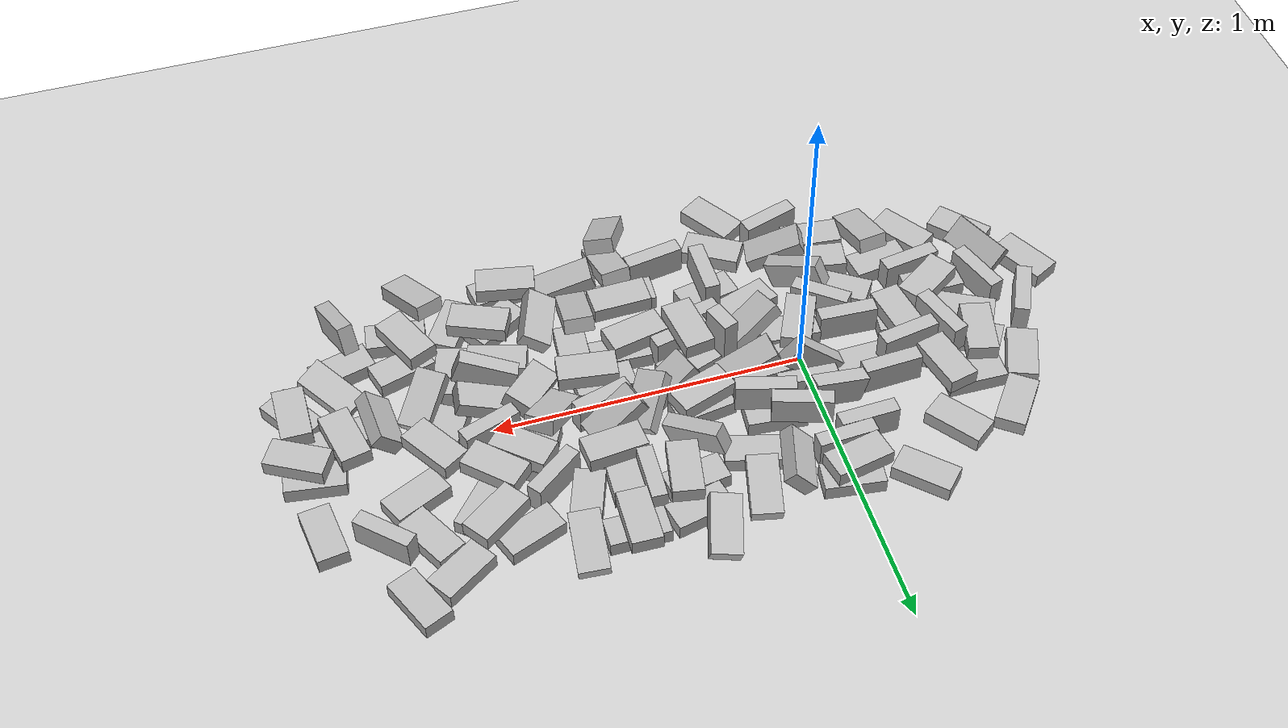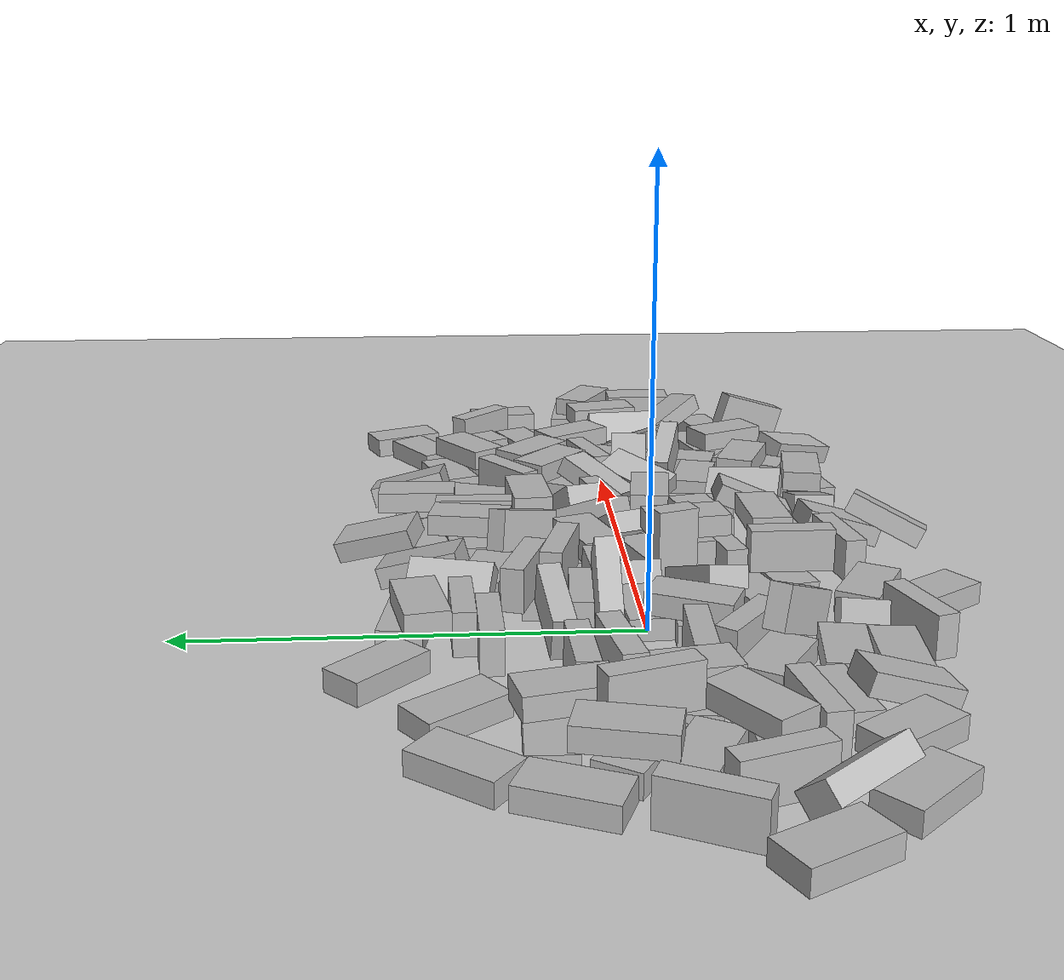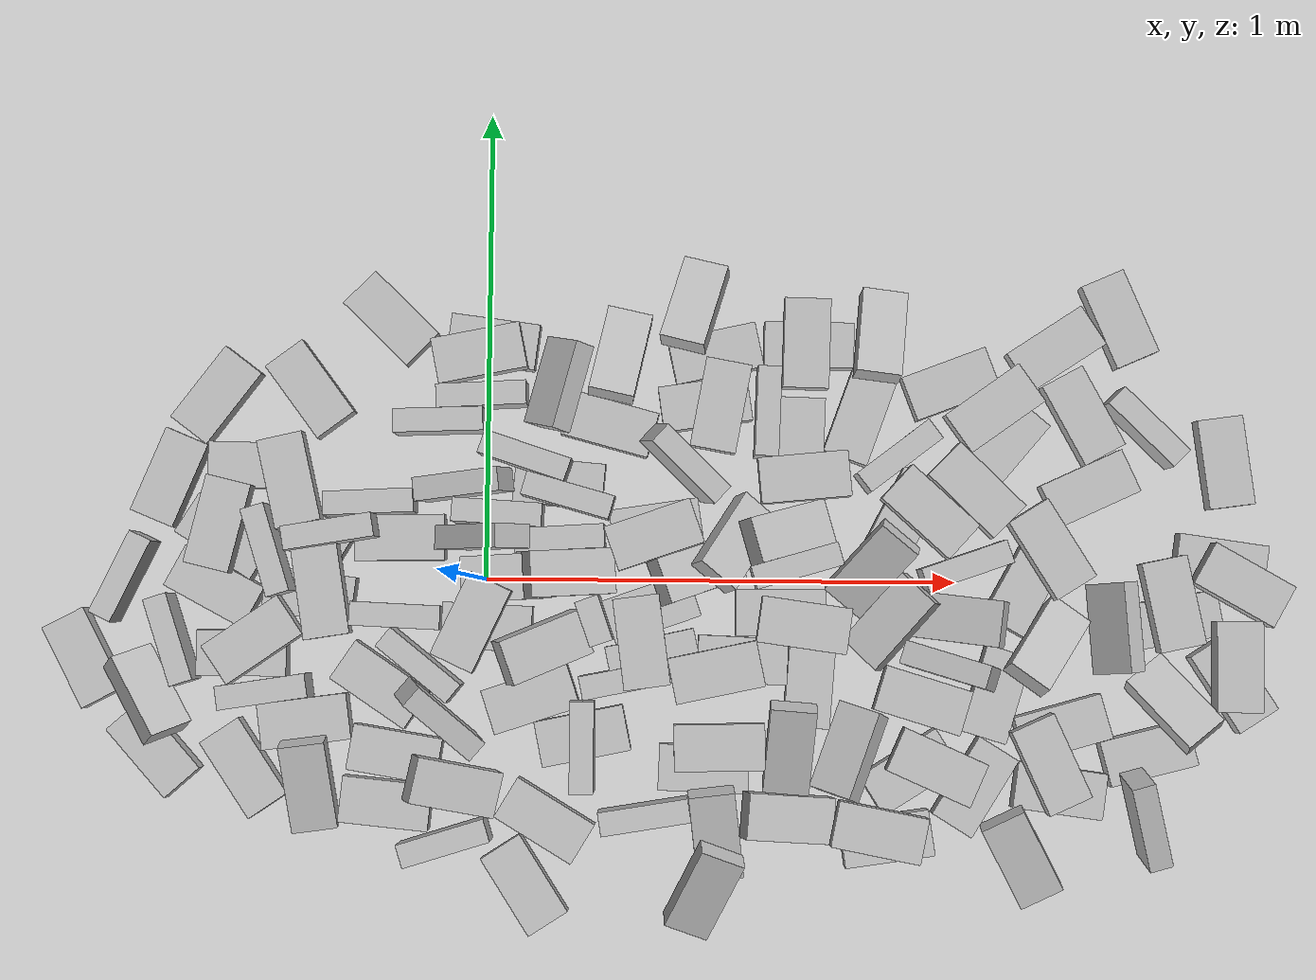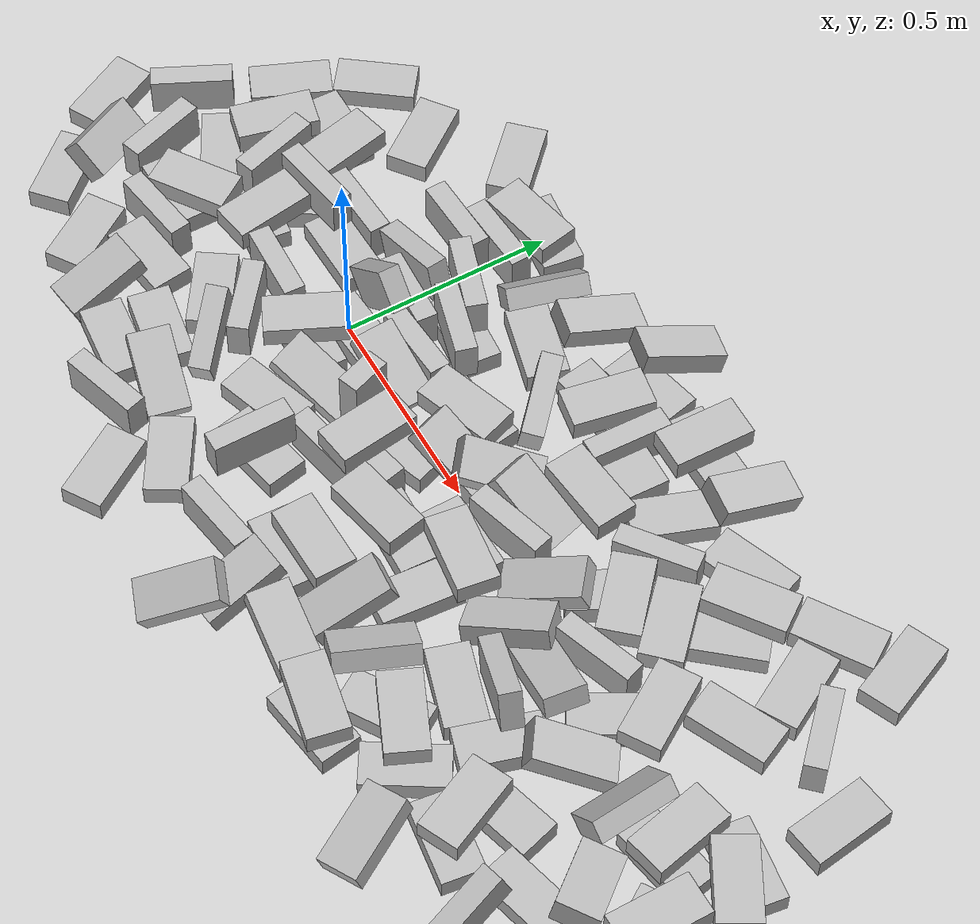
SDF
<sdf version="1.6">
 <world name="default">
  <light name="sun" type="directional">
   <pose>0 0 10 0 -0 0</pose>
   <diffuse>0.8 0.8 0.8 1</diffuse>
   <specular>0.2 0.2 0.2 1</specular>
   <attenuation>
    <range>1000</range>
    <constant>0.9</constant>
    <linear>0.01</linear>
    <quadratic>0.001</quadratic>
   </attenuation>
   <direction>-0.5 0.1 -0.9</direction>
  </light>
  <model name="ground_plane">
   <static>1</static>
   <link name="link">
    <collision name="collision">
     <geometry><plane><normal>0 0 1</normal><size>100 100</size></plane></geometry>
     <surface>
      <contact><collide_bitmask>65535</collide_bitmask></contact>
      <friction><ode><mu>100</mu><mu2>50</mu2></ode></friction>
     </surface>
    </collision>
    <visual name="visual">
     <cast_shadows>0</cast_shadows>
     <geometry><plane><normal>0 0 1</normal><size>100 100</size></plane></geometry>
     <material>
      <script><uri>file://media/materials/scripts/gazebo.material</uri><name>Gazebo/Grey</name></script>
     </material>
    </visual>
   </link>
  </model>
  <gravity>0 0 -9.8</gravity>
  <magnetic_field>6e-06 2.3e-05 -4.2e-05</magnetic_field>
  <atmosphere type="adiabatic"/>
  <physics name="default_physics" default="0" type="ode">
   <max_step_size>0.001</max_step_size>
   <real_time_factor>1</real_time_factor>
   <real_time_update_rate>1000</real_time_update_rate>
  </physics>
  <scene><ambient>0.4 0.4 0.4 1</ambient><background>0.7 0.7 0.7 1</background><shadows>1</shadows></scene>
  <spherical_coordinates>
   <surface_model>EARTH_WGS84</surface_model>
   <latitude_deg>0</latitude_deg>
   <longitude_deg>0</longitude_deg>
   <elevation>0</elevation>
   <heading_deg>0</heading_deg>
  </spherical_coordinates>
  <model name="dbrick_clone">
   <static>0</static>
   <self_collide>1</self_collide>
   <link name="link">
    <inertial>
     <mass>2</mass>
     <inertia>
      <ixx>0.0198483</ixx>
      <ixy>0</ixy>
      <ixz>0</ixz>
      <iyy>0.0643333</iyy>
      <iyz>0</iyz>
      <izz>0.0758483</izz>
     </inertia>
    </inertial>
    <collision name="dbrickC"><geometry><box><size>0.19 0.05 0.097</size></box></geometry></collision>
    <visual name="dbrickV">
     <cast_shadows>0</cast_shadows>
     <geometry><box><size>0.19 0.05 0.097</size></box></geometry>
     <material>
      <script>
       <uri>model://dbrick/materials/scripts</uri>
       <uri>model://dbrick/materials/textures</uri>
       <name>vrc/dbrick</name>
      </script>
     </material>
    </visual>
    <self_collide>1</self_collide>
   </link>
   <pose>-0.133609 -0.183068 0.0485 1.1e-05 -0 -0.672185</pose>
  </model>
  <model name="dbrick_clone_0">
   <static>0</static>
   <self_collide>1</self_collide>
   <link name="link">
    <inertial>
     <mass>2</mass>
     <inertia>
      <ixx>0.0198483</ixx>
      <ixy>0</ixy>
      <ixz>0</ixz>
      <iyy>0.0643333</iyy>
      <iyz>0</iyz>
      <izz>0.0758483</izz>
     </inertia>
    </inertial>
    <collision name="dbrickC"><geometry><box><size>0.19 0.05 0.097</size></box></geometry></collision>
    <visual name="dbrickV">
     <cast_shadows>0</cast_shadows>
     <geometry><box><size>0.19 0.05 0.097</size></box></geometry>
     <material>
      <script>
       <uri>model://dbrick/materials/scripts</uri>
       <uri>model://dbrick/materials/textures</uri>
       <name>vrc/dbrick</name>
      </script>
     </material>
    </visual>
    <self_collide>1</self_collide>
   </link>
   <pose>-0.087778 -0.29454 0.081286 -0.049423 0.378819 -0.722818</pose>
  </model>
  <model name="dbrick_clone_1">
   <static>0</static>
   <self_collide>1</self_collide>
   <link name="link">
    <inertial>
     <mass>2</mass>
     <inertia>
      <ixx>0.0198483</ixx>
      <ixy>0</ixy>
      <ixz>0</ixz>
      <iyy>0.0643333</iyy>
      <iyz>0</iyz>
      <izz>0.0758483</izz>
     </inertia>
    </inertial>
    <collision name="dbrickC"><geometry><box><size>0.19 0.05 0.097</size></box></geometry></collision>
    <visual name="dbrickV">
     <cast_shadows>0</cast_shadows>
     <geometry><box><size>0.19 0.05 0.097</size></box></geometry>
     <material>
      <script>
       <uri>model://dbrick/materials/scripts</uri>
       <uri>model://dbrick/materials/textures</uri>
       <name>vrc/dbrick</name>
      </script>
     </material>
    </visual>
    <self_collide>1</self_collide>
   </link>
   <pose>-0.046764 0.197802 0.072143 -0.000118 -0.27085 0.119844</pose>
  </model>
  <model name="dbrick_clone_2">
   <static>0</static>
   <self_collide>1</self_collide>
   <link name="link">
    <inertial>
     <mass>2</mass>
     <inertia>
      <ixx>0.0198483</ixx>
      <ixy>0</ixy>
      <ixz>0</ixz>
      <iyy>0.0643333</iyy>
      <iyz>0</iyz>
      <izz>0.0758483</izz>
     </inertia>
    </inertial>
    <collision name="dbrickC"><geometry><box><size>0.19 0.05 0.097</size></box></geometry></collision>
    <visual name="dbrickV">
     <cast_shadows>0</cast_shadows>
     <geometry><box><size>0.19 0.05 0.097</size></box></geometry>
     <material>
      <script>
       <uri>model://dbrick/materials/scripts</uri>
       <uri>model://dbrick/materials/textures</uri>
       <name>vrc/dbrick</name>
      </script>
     </material>
    </visual>
    <self_collide>1</self_collide>
   </link>
   <pose>0.299765 -0.209694 0.0485 -4e-06 1e-06 0.200864</pose>
  </model>
  <model name="dbrick_clone_3">
   <static>0</static>
   <self_collide>1</self_collide>
   <link name="link">
    <inertial>
     <mass>2</mass>
     <inertia>
      <ixx>0.0198483</ixx>
      <ixy>0</ixy>
      <ixz>0</ixz>
      <iyy>0.0643333</iyy>
      <iyz>0</iyz>
      <izz>0.0758483</izz>
     </inertia>
    </inertial>
    <collision name="dbrickC"><geometry><box><size>0.19 0.05 0.097</size></box></geometry></collision>
    <visual name="dbrickV">
     <cast_shadows>0</cast_shadows>
     <geometry><box><size>0.19 0.05 0.097</size></box></geometry>
     <material>
      <script>
       <uri>model://dbrick/materials/scripts</uri>
       <uri>model://dbrick/materials/textures</uri>
       <name>vrc/dbrick</name>
      </script>
     </material>
    </visual>
    <self_collide>1</self_collide>
   </link>
   <pose>-0.076343 -0.552308 0.048479 1e-06 -2.3e-05 0.301755</pose>
  </model>
  <model name="dbrick_clone_4">
   <static>0</static>
   <self_collide>1</self_collide>
   <link name="link">
    <inertial>
     <mass>2</mass>
     <inertia>
      <ixx>0.0198483</ixx>
      <ixy>0</ixy>
      <ixz>0</ixz>
      <iyy>0.0643333</iyy>
      <iyz>0</iyz>
      <izz>0.0758483</izz>
     </inertia>
    </inertial>
    <collision name="dbrickC"><geometry><box><size>0.19 0.05 0.097</size></box></geometry></collision>
    <visual name="dbrickV">
     <cast_shadows>0</cast_shadows>
     <geometry><box><size>0.19 0.05 0.097</size></box></geometry>
     <material>
      <script>
       <uri>model://dbrick/materials/scripts</uri>
       <uri>model://dbrick/materials/textures</uri>
       <name>vrc/dbrick</name>
      </script>
     </material>
    </visual>
    <self_collide>1</self_collide>
   </link>
   <pose>-0.658381 -0.134313 0.048502 -6.1e-05 -0 -1.24975</pose>
  </model>
  <model name="dbrick_clone_6">
   <static>0</static>
   <self_collide>1</self_collide>
   <link name="link">
    <inertial>
     <mass>2</mass>
     <inertia>
      <ixx>0.0198483</ixx>
      <ixy>0</ixy>
      <ixz>0</ixz>
      <iyy>0.0643333</iyy>
      <iyz>0</iyz>
      <izz>0.0758483</izz>
     </inertia>
    </inertial>
    <collision name="dbrickC"><geometry><box><size>0.19 0.05 0.097</size></box></geometry></collision>
    <visual name="dbrickV">
     <cast_shadows>0</cast_shadows>
     <geometry><box><size>0.19 0.05 0.097</size></box></geometry>
     <material>
      <script>
       <uri>model://dbrick/materials/scripts</uri>
       <uri>model://dbrick/materials/textures</uri>
       <name>vrc/dbrick</name>
      </script>
     </material>
    </visual>
    <self_collide>1</self_collide>
   </link>
   <pose>-0.244631 0.159161 0.048498 -0 2.1e-05 0.049077</pose>
  </model>
  <model name="dbrick_clone_7">
   <static>0</static>
   <self_collide>1</self_collide>
   <link name="link">
    <inertial>
     <mass>2</mass>
     <inertia>
      <ixx>0.0198483</ixx>
      <ixy>0</ixy>
      <ixz>0</ixz>
      <iyy>0.0643333</iyy>
      <iyz>0</iyz>
      <izz>0.0758483</izz>
     </inertia>
    </inertial>
    <collision name="dbrickC"><geometry><box><size>0.19 0.05 0.097</size></box></geometry></collision>
    <visual name="dbrickV">
     <cast_shadows>0</cast_shadows>
     <geometry><box><size>0.19 0.05 0.097</size></box></geometry>
     <material>
      <script>
       <uri>model://dbrick/materials/scripts</uri>
       <uri>model://dbrick/materials/textures</uri>
       <name>vrc/dbrick</name>
      </script>
     </material>
    </visual>
    <self_collide>1</self_collide>
   </link>
   <pose>-0.460959 -0.241476 0.0485 0 -0 0.154159</pose>
  </model>
  <model name="dbrick_clone_8">
   <static>0</static>
   <self_collide>1</self_collide>
   <link name="link">
    <inertial>
     <mass>2</mass>
     <inertia>
      <ixx>0.0198483</ixx>
      <ixy>0</ixy>
      <ixz>0</ixz>
      <iyy>0.0643333</iyy>
      <iyz>0</iyz>
      <izz>0.0758483</izz>
     </inertia>
    </inertial>
    <collision name="dbrickC"><geometry><box><size>0.19 0.05 0.097</size></box></geometry></collision>
    <visual name="dbrickV">
     <cast_shadows>0</cast_shadows>
     <geometry><box><size>0.19 0.05 0.097</size></box></geometry>
     <material>
      <script>
       <uri>model://dbrick/materials/scripts</uri>
       <uri>model://dbrick/materials/textures</uri>
       <name>vrc/dbrick</name>
      </script>
     </material>
    </visual>
    <self_collide>1</self_collide>
   </link>
   <pose>-0.383635 0.096606 0.024997 -1.57074 2e-06 -0.535232</pose>
  </model>
  <model name="dbrick_clone_9">
   <static>0</static>
   <self_collide>1</self_collide>
   <link name="link">
    <inertial>
     <mass>2</mass>
     <inertia>
      <ixx>0.0198483</ixx>
      <ixy>0</ixy>
      <ixz>0</ixz>
      <iyy>0.0643333</iyy>
      <iyz>0</iyz>
      <izz>0.0758483</izz>
     </inertia>
    </inertial>
    <collision name="dbrickC"><geometry><box><size>0.19 0.05 0.097</size></box></geometry></collision>
    <visual name="dbrickV">
     <cast_shadows>0</cast_shadows>
     <geometry><box><size>0.19 0.05 0.097</size></box></geometry>
     <material>
      <script>
       <uri>model://dbrick/materials/scripts</uri>
       <uri>model://dbrick/materials/textures</uri>
       <name>vrc/dbrick</name>
      </script>
     </material>
    </visual>
    <self_collide>1</self_collide>
   </link>
   <pose>0.342479 -0.494706 0.0485 0 -0 0.163884</pose>
  </model>
  <model name="dbrick_clone_10">
   <static>0</static>
   <self_collide>1</self_collide>
   <link name="link">
    <inertial>
     <mass>2</mass>
     <inertia>
      <ixx>0.0198483</ixx>
      <ixy>0</ixy>
      <ixz>0</ixz>
      <iyy>0.0643333</iyy>
      <iyz>0</iyz>
      <izz>0.0758483</izz>
     </inertia>
    </inertial>
    <collision name="dbrickC"><geometry><box><size>0.19 0.05 0.097</size></box></geometry></collision>
    <visual name="dbrickV">
     <cast_shadows>0</cast_shadows>
     <geometry><box><size>0.19 0.05 0.097</size></box></geometry>
     <material>
      <script>
       <uri>model://dbrick/materials/scripts</uri>
       <uri>model://dbrick/materials/textures</uri>
       <name>vrc/dbrick</name>
      </script>
     </material>
    </visual>
    <self_collide>1</self_collide>
   </link>
   <pose>0.004749 -0.102029 0.024998 -1.57084 -3e-06 -0.044556</pose>
  </model>
  <model name="dbrick_clone_12">
   <static>0</static>
   <self_collide>1</self_collide>
   <link name="link">
    <inertial>
     <mass>2</mass>
     <inertia>
      <ixx>0.0198483</ixx>
      <ixy>0</ixy>
      <ixz>0</ixz>
      <iyy>0.0643333</iyy>
      <iyz>0</iyz>
      <izz>0.0758483</izz>
     </inertia>
    </inertial>
    <collision name="dbrickC"><geometry><box><size>0.19 0.05 0.097</size></box></geometry></collision>
    <visual name="dbrickV">
     <cast_shadows>0</cast_shadows>
     <geometry><box><size>0.19 0.05 0.097</size></box></geometry>
     <material>
      <script>
       <uri>model://dbrick/materials/scripts</uri>
       <uri>model://dbrick/materials/textures</uri>
       <name>vrc/dbrick</name>
      </script>
     </material>
    </visual>
    <self_collide>1</self_collide>
   </link>
   <pose>0.026004 0.139546 0.048479 -2.2e-05 -2.1e-05 -0.058536</pose>
  </model>
  <model name="dbrick_clone_13">
   <static>0</static>
   <self_collide>1</self_collide>
   <link name="link">
    <inertial>
     <mass>2</mass>
     <inertia>
      <ixx>0.0198483</ixx>
      <ixy>0</ixy>
      <ixz>0</ixz>
      <iyy>0.0643333</iyy>
      <iyz>0</iyz>
      <izz>0.0758483</izz>
     </inertia>
    </inertial>
    <collision name="dbrickC"><geometry><box><size>0.19 0.05 0.097</size></box></geometry></collision>
    <visual name="dbrickV">
     <cast_shadows>0</cast_shadows>
     <geometry><box><size>0.19 0.05 0.097</size></box></geometry>
     <material>
      <script>
       <uri>model://dbrick/materials/scripts</uri>
       <uri>model://dbrick/materials/textures</uri>
       <name>vrc/dbrick</name>
      </script>
     </material>
    </visual>
    <self_collide>1</self_collide>
   </link>
   <pose>-0.185448 -0.370894 0.025 -1.5708 -0 -0.163132</pose>
  </model>
  <model name="dbrick_clone_14">
   <static>0</static>
   <self_collide>1</self_collide>
   <link name="link">
    <inertial>
     <mass>2</mass>
     <inertia>
      <ixx>0.0198483</ixx>
      <ixy>0</ixy>
      <ixz>0</ixz>
      <iyy>0.0643333</iyy>
      <iyz>0</iyz>
      <izz>0.0758483</izz>
     </inertia>
    </inertial>
    <collision name="dbrickC"><geometry><box><size>0.19 0.05 0.097</size></box></geometry></collision>
    <visual name="dbrickV">
     <cast_shadows>0</cast_shadows>
     <geometry><box><size>0.19 0.05 0.097</size></box></geometry>
     <material>
      <script>
       <uri>model://dbrick/materials/scripts</uri>
       <uri>model://dbrick/materials/textures</uri>
       <name>vrc/dbrick</name>
      </script>
     </material>
    </visual>
    <self_collide>1</self_collide>
   </link>
   <pose>-0.024426 -0.092165 0.075 -1.57076 4.6e-05 -2.00529</pose>
  </model>
  <model name="dbrick_0">
   <static>0</static>
   <self_collide>1</self_collide>
   <link name="link">
    <inertial>
     <mass>2</mass>
     <inertia>
      <ixx>0.0198483</ixx>
      <ixy>0</ixy>
      <ixz>0</ixz>
      <iyy>0.0643333</iyy>
      <iyz>0</iyz>
      <izz>0.0758483</izz>
     </inertia>
    </inertial>
    <collision name="dbrickC"><geometry><box><size>0.19 0.05 0.097</size></box></geometry></collision>
    <visual name="dbrickV">
     <cast_shadows>0</cast_shadows>
     <geometry><box><size>0.19 0.05 0.097</size></box></geometry>
     <material>
      <script>
       <uri>model://dbrick/materials/scripts</uri>
       <uri>model://dbrick/materials/textures</uri>
       <name>vrc/dbrick</name>
      </script>
     </material>
    </visual>
    <self_collide>1</self_collide>
   </link>
   <pose>-0.003689 0.086742 0.100943 3.14132 0.769792 -3.13146</pose>
  </model>
  <model name="dbrick_1">
   <static>0</static>
   <self_collide>1</self_collide>
   <link name="link">
    <inertial>
     <mass>2</mass>
     <inertia>
      <ixx>0.0198483</ixx>
      <ixy>0</ixy>
      <ixz>0</ixz>
      <iyy>0.0643333</iyy>
      <iyz>0</iyz>
      <izz>0.0758483</izz>
     </inertia>
    </inertial>
    <collision name="dbrickC"><geometry><box><size>0.19 0.05 0.097</size></box></geometry></collision>
    <visual name="dbrickV">
     <cast_shadows>0</cast_shadows>
     <geometry><box><size>0.19 0.05 0.097</size></box></geometry>
     <material>
      <script>
       <uri>model://dbrick/materials/scripts</uri>
       <uri>model://dbrick/materials/textures</uri>
       <name>vrc/dbrick</name>
      </script>
     </material>
    </visual>
    <self_collide>1</self_collide>
   </link>
   <pose>-0.184451 -0.079483 0.048481 1.1e-05 -0 -0.043888</pose>
  </model>
  <model name="dbrick_clone_10_clone_0">
   <static>0</static>
   <self_collide>1</self_collide>
   <link name="link">
    <inertial>
     <mass>2</mass>
     <inertia>
      <ixx>0.0198483</ixx>
      <ixy>0</ixy>
      <ixz>0</ixz>
      <iyy>0.0643333</iyy>
      <iyz>0</iyz>
      <izz>0.0758483</izz>
     </inertia>
    </inertial>
    <collision name="dbrickC"><geometry><box><size>0.19 0.05 0.097</size></box></geometry></collision>
    <visual name="dbrickV">
     <cast_shadows>0</cast_shadows>
     <geometry><box><size>0.19 0.05 0.097</size></box></geometry>
     <material>
      <script>
       <uri>model://dbrick/materials/scripts</uri>
       <uri>model://dbrick/materials/textures</uri>
       <name>vrc/dbrick</name>
      </script>
     </material>
    </visual>
    <self_collide>1</self_collide>
   </link>
   <pose>-0.372297 -0.036682 0.025 -1.5708 3e-06 -0.125776</pose>
  </model>
  <model name="dbrick_clone_10_clone_1">
   <static>0</static>
   <self_collide>1</self_collide>
   <link name="link">
    <inertial>
     <mass>2</mass>
     <inertia>
      <ixx>0.0198483</ixx>
      <ixy>0</ixy>
      <ixz>0</ixz>
      <iyy>0.0643333</iyy>
      <iyz>0</iyz>
      <izz>0.0758483</izz>
     </inertia>
    </inertial>
    <collision name="dbrickC"><geometry><box><size>0.19 0.05 0.097</size></box></geometry></collision>
    <visual name="dbrickV">
     <cast_shadows>0</cast_shadows>
     <geometry><box><size>0.19 0.05 0.097</size></box></geometry>
     <material>
      <script>
       <uri>model://dbrick/materials/scripts</uri>
       <uri>model://dbrick/materials/textures</uri>
       <name>vrc/dbrick</name>
      </script>
     </material>
    </visual>
    <self_collide>1</self_collide>
   </link>
   <pose>-0.181742 0.085627 0.024822 -1.57076 -0 0.018671</pose>
  </model>
  <model name="dbrick_clone_10_clone_3">
   <static>0</static>
   <self_collide>1</self_collide>
   <link name="link">
    <inertial>
     <mass>2</mass>
     <inertia>
      <ixx>0.0198483</ixx>
      <ixy>0</ixy>
      <ixz>0</ixz>
      <iyy>0.0643333</iyy>
      <iyz>0</iyz>
      <izz>0.0758483</izz>
     </inertia>
    </inertial>
    <collision name="dbrickC"><geometry><box><size>0.19 0.05 0.097</size></box></geometry></collision>
    <visual name="dbrickV">
     <cast_shadows>0</cast_shadows>
     <geometry><box><size>0.19 0.05 0.097</size></box></geometry>
     <material>
      <script>
       <uri>model://dbrick/materials/scripts</uri>
       <uri>model://dbrick/materials/textures</uri>
       <name>vrc/dbrick</name>
      </script>
     </material>
    </visual>
    <self_collide>1</self_collide>
   </link>
   <pose>0.154282 0.204825 0.025 -1.57079 -0 -0.08803</pose>
  </model>
  <model name="dbrick_clone_10_clone_5">
   <static>0</static>
   <self_collide>1</self_collide>
   <link name="link">
    <inertial>
     <mass>2</mass>
     <inertia>
      <ixx>0.0198483</ixx>
      <ixy>0</ixy>
      <ixz>0</ixz>
      <iyy>0.0643333</iyy>
      <iyz>0</iyz>
      <izz>0.0758483</izz>
     </inertia>
    </inertial>
    <collision name="dbrickC"><geometry><box><size>0.19 0.05 0.097</size></box></geometry></collision>
    <visual name="dbrickV">
     <cast_shadows>0</cast_shadows>
     <geometry><box><size>0.19 0.05 0.097</size></box></geometry>
     <material>
      <script>
       <uri>model://dbrick/materials/scripts</uri>
       <uri>model://dbrick/materials/textures</uri>
       <name>vrc/dbrick</name>
      </script>
     </material>
    </visual>
    <self_collide>1</self_collide>
   </link>
   <pose>-0.512018 -0.161329 0.024994 -1.57081 3.2e-05 0.005484</pose>
  </model>
  <model name="dbrick_clone_10_clone_6_clone">
   <static>0</static>
   <self_collide>1</self_collide>
   <link name="link">
    <inertial>
     <mass>2</mass>
     <inertia>
      <ixx>0.0198483</ixx>
      <ixy>0</ixy>
      <ixz>0</ixz>
      <iyy>0.0643333</iyy>
      <iyz>0</iyz>
      <izz>0.0758483</izz>
     </inertia>
    </inertial>
    <collision name="dbrickC"><geometry><box><size>0.19 0.05 0.097</size></box></geometry></collision>
    <visual name="dbrickV">
     <cast_shadows>0</cast_shadows>
     <geometry><box><size>0.19 0.05 0.097</size></box></geometry>
     <material>
      <script>
       <uri>model://dbrick/materials/scripts</uri>
       <uri>model://dbrick/materials/textures</uri>
       <name>vrc/dbrick</name>
      </script>
     </material>
    </visual>
    <self_collide>1</self_collide>
   </link>
   <pose>0.158145 0.086479 0.048471 2e-06 -1e-06 0.064436</pose>
  </model>
  <model name="dbrick_clone_10_clone_6_clone_0">
   <static>0</static>
   <self_collide>1</self_collide>
   <link name="link">
    <inertial>
     <mass>2</mass>
     <inertia>
      <ixx>0.0198483</ixx>
      <ixy>0</ixy>
      <ixz>0</ixz>
      <iyy>0.0643333</iyy>
      <iyz>0</iyz>
      <izz>0.0758483</izz>
     </inertia>
    </inertial>
    <collision name="dbrickC"><geometry><box><size>0.19 0.05 0.097</size></box></geometry></collision>
    <visual name="dbrickV">
     <cast_shadows>0</cast_shadows>
     <geometry><box><size>0.19 0.05 0.097</size></box></geometry>
     <material>
      <script>
       <uri>model://dbrick/materials/scripts</uri>
       <uri>model://dbrick/materials/textures</uri>
       <name>vrc/dbrick</name>
      </script>
     </material>
    </visual>
    <self_collide>1</self_collide>
   </link>
   <pose>0.261087 0.331677 0.024857 -1.5708 0.000137 -0.261447</pose>
  </model>
  <model name="dbrick_clone_10_clone_6_clone_1">
   <static>0</static>
   <self_collide>1</self_collide>
   <link name="link">
    <inertial>
     <mass>2</mass>
     <inertia>
      <ixx>0.0198483</ixx>
      <ixy>0</ixy>
      <ixz>0</ixz>
      <iyy>0.0643333</iyy>
      <iyz>0</iyz>
      <izz>0.0758483</izz>
     </inertia>
    </inertial>
    <collision name="dbrickC"><geometry><box><size>0.19 0.05 0.097</size></box></geometry></collision>
    <visual name="dbrickV">
     <cast_shadows>0</cast_shadows>
     <geometry><box><size>0.19 0.05 0.097</size></box></geometry>
     <material>
      <script>
       <uri>model://dbrick/materials/scripts</uri>
       <uri>model://dbrick/materials/textures</uri>
       <name>vrc/dbrick</name>
      </script>
     </material>
    </visual>
    <self_collide>1</self_collide>
   </link>
   <pose>0.09986 -0.252551 0.024997 1.5708 2.9e-05 0.324917</pose>
  </model>
  <model name="dbrick_clone_10_clone_6_clone_2">
   <static>0</static>
   <self_collide>1</self_collide>
   <link name="link">
    <inertial>
     <mass>2</mass>
     <inertia>
      <ixx>0.0198483</ixx>
      <ixy>0</ixy>
      <ixz>0</ixz>
      <iyy>0.0643333</iyy>
      <iyz>0</iyz>
      <izz>0.0758483</izz>
     </inertia>
    </inertial>
    <collision name="dbrickC"><geometry><box><size>0.19 0.05 0.097</size></box></geometry></collision>
    <visual name="dbrickV">
     <cast_shadows>0</cast_shadows>
     <geometry><box><size>0.19 0.05 0.097</size></box></geometry>
     <material>
      <script>
       <uri>model://dbrick/materials/scripts</uri>
       <uri>model://dbrick/materials/textures</uri>
       <name>vrc/dbrick</name>
      </script>
     </material>
    </visual>
    <self_collide>1</self_collide>
   </link>
   <pose>-0.340802 -0.031051 0.074988 -1.57075 7.7e-05 -1.41024</pose>
  </model>
  <model name="dbrick_clone_10_clone_6_clone_3">
   <static>0</static>
   <self_collide>1</self_collide>
   <link name="link">
    <inertial>
     <mass>2</mass>
     <inertia>
      <ixx>0.0198483</ixx>
      <ixy>0</ixy>
      <ixz>0</ixz>
      <iyy>0.0643333</iyy>
      <iyz>0</iyz>
      <izz>0.0758483</izz>
     </inertia>
    </inertial>
    <collision name="dbrickC"><geometry><box><size>0.19 0.05 0.097</size></box></geometry></collision>
    <visual name="dbrickV">
     <cast_shadows>0</cast_shadows>
     <geometry><box><size>0.19 0.05 0.097</size></box></geometry>
     <material>
      <script>
       <uri>model://dbrick/materials/scripts</uri>
       <uri>model://dbrick/materials/textures</uri>
       <name>vrc/dbrick</name>
      </script>
     </material>
    </visual>
    <self_collide>1</self_collide>
   </link>
   <pose>-0.377452 -0.304613 0.025001 -1.57081 -0 0.136091</pose>
  </model>
  <model name="dbrick_clone_10_clone_6_clone_4">
   <static>0</static>
   <self_collide>1</self_collide>
   <link name="link">
    <inertial>
     <mass>2</mass>
     <inertia>
      <ixx>0.0198483</ixx>
      <ixy>0</ixy>
      <ixz>0</ixz>
      <iyy>0.0643333</iyy>
      <iyz>0</iyz>
      <izz>0.0758483</izz>
     </inertia>
    </inertial>
    <collision name="dbrickC"><geometry><box><size>0.19 0.05 0.097</size></box></geometry></collision>
    <visual name="dbrickV">
     <cast_shadows>0</cast_shadows>
     <geometry><box><size>0.19 0.05 0.097</size></box></geometry>
     <material>
      <script>
       <uri>model://dbrick/materials/scripts</uri>
       <uri>model://dbrick/materials/textures</uri>
       <name>vrc/dbrick</name>
      </script>
     </material>
    </visual>
    <self_collide>1</self_collide>
   </link>
   <pose>-0.059828 -0.436128 0.06038 -1.57069 0.404573 -0.21265</pose>
  </model>
  <model name="dbrick_clone_10_clone_6_clone_1_clone_0">
   <static>0</static>
   <self_collide>1</self_collide>
   <link name="link">
    <inertial>
     <mass>2</mass>
     <inertia>
      <ixx>0.0198483</ixx>
      <ixy>0</ixy>
      <ixz>0</ixz>
      <iyy>0.0643333</iyy>
      <iyz>0</iyz>
      <izz>0.0758483</izz>
     </inertia>
    </inertial>
    <collision name="dbrickC"><geometry><box><size>0.19 0.05 0.097</size></box></geometry></collision>
    <visual name="dbrickV">
     <cast_shadows>0</cast_shadows>
     <geometry><box><size>0.19 0.05 0.097</size></box></geometry>
     <material>
      <script>
       <uri>model://dbrick/materials/scripts</uri>
       <uri>model://dbrick/materials/textures</uri>
       <name>vrc/dbrick</name>
      </script>
     </material>
    </visual>
    <self_collide>1</self_collide>
   </link>
   <pose>0.354362 -0.145673 0.048498 -3.14158 -2e-05 0.220302</pose>
  </model>
  <model name="dbrick_clone_10_clone_6_clone_1_clone_1">
   <static>0</static>
   <self_collide>1</self_collide>
   <link name="link">
    <inertial>
     <mass>2</mass>
     <inertia>
      <ixx>0.0198483</ixx>
      <ixy>0</ixy>
      <ixz>0</ixz>
      <iyy>0.0643333</iyy>
      <iyz>0</iyz>
      <izz>0.0758483</izz>
     </inertia>
    </inertial>
    <collision name="dbrickC"><geometry><box><size>0.19 0.05 0.097</size></box></geometry></collision>
    <visual name="dbrickV">
     <cast_shadows>0</cast_shadows>
     <geometry><box><size>0.19 0.05 0.097</size></box></geometry>
     <material>
      <script>
       <uri>model://dbrick/materials/scripts</uri>
       <uri>model://dbrick/materials/textures</uri>
       <name>vrc/dbrick</name>
      </script>
     </material>
    </visual>
    <self_collide>1</self_collide>
   </link>
   <pose>0.125402 -0.142849 0.065373 1.74398 0.373455 0.402562</pose>
  </model>
  <model name="dbrick_clone_10_clone_6_clone_1_clone_2">
   <static>0</static>
   <self_collide>1</self_collide>
   <link name="link">
    <inertial>
     <mass>2</mass>
     <inertia>
      <ixx>0.0198483</ixx>
      <ixy>0</ixy>
      <ixz>0</ixz>
      <iyy>0.0643333</iyy>
      <iyz>0</iyz>
      <izz>0.0758483</izz>
     </inertia>
    </inertial>
    <collision name="dbrickC"><geometry><box><size>0.19 0.05 0.097</size></box></geometry></collision>
    <visual name="dbrickV">
     <cast_shadows>0</cast_shadows>
     <geometry><box><size>0.19 0.05 0.097</size></box></geometry>
     <material>
      <script>
       <uri>model://dbrick/materials/scripts</uri>
       <uri>model://dbrick/materials/textures</uri>
       <name>vrc/dbrick</name>
      </script>
     </material>
    </visual>
    <self_collide>1</self_collide>
   </link>
   <pose>0.210105 -0.329515 0.025 1.5708 0 0.203738</pose>
  </model>
  <model name="dbrick_clone_10_clone_6_clone_1_clone_3">
   <static>0</static>
   <self_collide>1</self_collide>
   <link name="link">
    <inertial>
     <mass>2</mass>
     <inertia>
      <ixx>0.0198483</ixx>
      <ixy>0</ixy>
      <ixz>0</ixz>
      <iyy>0.0643333</iyy>
      <iyz>0</iyz>
      <izz>0.0758483</izz>
     </inertia>
    </inertial>
    <collision name="dbrickC"><geometry><box><size>0.19 0.05 0.097</size></box></geometry></collision>
    <visual name="dbrickV">
     <cast_shadows>0</cast_shadows>
     <geometry><box><size>0.19 0.05 0.097</size></box></geometry>
     <material>
      <script>
       <uri>model://dbrick/materials/scripts</uri>
       <uri>model://dbrick/materials/textures</uri>
       <name>vrc/dbrick</name>
      </script>
     </material>
    </visual>
    <self_collide>1</self_collide>
   </link>
   <pose>0.178595 0.014141 0.059911 1.57079 0.398828 0.064411</pose>
  </model>
  <model name="dbrick_clone_10_clone_6_clone_1_clone_4">
   <static>0</static>
   <self_collide>1</self_collide>
   <link name="link">
    <inertial>
     <mass>2</mass>
     <inertia>
      <ixx>0.0198483</ixx>
      <ixy>0</ixy>
      <ixz>0</ixz>
      <iyy>0.0643333</iyy>
      <iyz>0</iyz>
      <izz>0.0758483</izz>
     </inertia>
    </inertial>
    <collision name="dbrickC"><geometry><box><size>0.19 0.05 0.097</size></box></geometry></collision>
    <visual name="dbrickV">
     <cast_shadows>0</cast_shadows>
     <geometry><box><size>0.19 0.05 0.097</size></box></geometry>
     <material>
      <script>
       <uri>model://dbrick/materials/scripts</uri>
       <uri>model://dbrick/materials/textures</uri>
       <name>vrc/dbrick</name>
      </script>
     </material>
    </visual>
    <self_collide>1</self_collide>
   </link>
   <pose>0.353139 -0.05945 0.025001 1.57084 1.6e-05 0.338845</pose>
  </model>
  <model name="dbrick_clone_10_clone_6_clone_1_clone_5">
   <static>0</static>
   <self_collide>1</self_collide>
   <link name="link">
    <inertial>
     <mass>2</mass>
     <inertia>
      <ixx>0.0198483</ixx>
      <ixy>0</ixy>
      <ixz>0</ixz>
      <iyy>0.0643333</iyy>
      <iyz>0</iyz>
      <izz>0.0758483</izz>
     </inertia>
    </inertial>
    <collision name="dbrickC"><geometry><box><size>0.19 0.05 0.097</size></box></geometry></collision>
    <visual name="dbrickV">
     <cast_shadows>0</cast_shadows>
     <geometry><box><size>0.19 0.05 0.097</size></box></geometry>
     <material>
      <script>
       <uri>model://dbrick/materials/scripts</uri>
       <uri>model://dbrick/materials/textures</uri>
       <name>vrc/dbrick</name>
      </script>
     </material>
    </visual>
    <self_collide>1</self_collide>
   </link>
   <pose>0.361903 0.113562 0.024998 1.57083 -0 0.151408</pose>
  </model>
  <model name="dbrick_clone_10_clone_6_clone_1_clone_6">
   <static>0</static>
   <self_collide>1</self_collide>
   <link name="link">
    <inertial>
     <mass>2</mass>
     <inertia>
      <ixx>0.0198483</ixx>
      <ixy>0</ixy>
      <ixz>0</ixz>
      <iyy>0.0643333</iyy>
      <iyz>0</iyz>
      <izz>0.0758483</izz>
     </inertia>
    </inertial>
    <collision name="dbrickC"><geometry><box><size>0.19 0.05 0.097</size></box></geometry></collision>
    <visual name="dbrickV">
     <cast_shadows>0</cast_shadows>
     <geometry><box><size>0.19 0.05 0.097</size></box></geometry>
     <material>
      <script>
       <uri>model://dbrick/materials/scripts</uri>
       <uri>model://dbrick/materials/textures</uri>
       <name>vrc/dbrick</name>
      </script>
     </material>
    </visual>
    <self_collide>1</self_collide>
   </link>
   <pose>-0.321636 0.094184 0.098508 0.000201 0.000142 0.166547</pose>
  </model>
  <model name="dbrick_clone_10_clone_6_clone_1_clone_8">
   <static>0</static>
   <self_collide>1</self_collide>
   <link name="link">
    <inertial>
     <mass>2</mass>
     <inertia>
      <ixx>0.0198483</ixx>
      <ixy>0</ixy>
      <ixz>0</ixz>
      <iyy>0.0643333</iyy>
      <iyz>0</iyz>
      <izz>0.0758483</izz>
     </inertia>
    </inertial>
    <collision name="dbrickC"><geometry><box><size>0.19 0.05 0.097</size></box></geometry></collision>
    <visual name="dbrickV">
     <cast_shadows>0</cast_shadows>
     <geometry><box><size>0.19 0.05 0.097</size></box></geometry>
     <material>
      <script>
       <uri>model://dbrick/materials/scripts</uri>
       <uri>model://dbrick/materials/textures</uri>
       <name>vrc/dbrick</name>
      </script>
     </material>
    </visual>
    <self_collide>1</self_collide>
   </link>
   <pose>-0.481375 -0.133363 0.074993 1.57079 2.8e-05 0.603379</pose>
  </model>
  <model name="dbrick_clone_clone">
   <static>0</static>
   <self_collide>1</self_collide>
   <link name="link">
    <inertial>
     <mass>2</mass>
     <inertia>
      <ixx>0.0198483</ixx>
      <ixy>0</ixy>
      <ixz>0</ixz>
      <iyy>0.0643333</iyy>
      <iyz>0</iyz>
      <izz>0.0758483</izz>
     </inertia>
    </inertial>
    <collision name="dbrickC"><geometry><box><size>0.19 0.05 0.097</size></box></geometry></collision>
    <visual name="dbrickV">
     <cast_shadows>0</cast_shadows>
     <geometry><box><size>0.19 0.05 0.097</size></box></geometry>
     <material>
      <script>
       <uri>model://dbrick/materials/scripts</uri>
       <uri>model://dbrick/materials/textures</uri>
       <name>vrc/dbrick</name>
      </script>
     </material>
    </visual>
    <self_collide>1</self_collide>
   </link>
   <pose>0.177164 0.174103 0.098498 3.3e-05 -1.9e-05 -0.271425</pose>
  </model>
  <model name="dbrick_clone_10_clone_6_clone_1_clone_clone">
   <static>0</static>
   <self_collide>1</self_collide>
   <link name="link">
    <inertial>
     <mass>2</mass>
     <inertia>
      <ixx>0.0198483</ixx>
      <ixy>0</ixy>
      <ixz>0</ixz>
      <iyy>0.0643333</iyy>
      <iyz>0</iyz>
      <izz>0.0758483</izz>
     </inertia>
    </inertial>
    <collision name="dbrickC"><geometry><box><size>0.19 0.05 0.097</size></box></geometry></collision>
    <visual name="dbrickV">
     <cast_shadows>0</cast_shadows>
     <geometry><box><size>0.19 0.05 0.097</size></box></geometry>
     <material>
      <script>
       <uri>model://dbrick/materials/scripts</uri>
       <uri>model://dbrick/materials/textures</uri>
       <name>vrc/dbrick</name>
      </script>
     </material>
    </visual>
    <self_collide>1</self_collide>
   </link>
   <pose>0.235621 -0.087015 0.095 -1.36001 1.57079 -2.59197</pose>
  </model>
  <model name="dbrick_clone_10_clone_6_clone_1_clone_clone_0">
   <static>0</static>
   <self_collide>1</self_collide>
   <link name="link">
    <inertial>
     <mass>2</mass>
     <inertia>
      <ixx>0.0198483</ixx>
      <ixy>0</ixy>
      <ixz>0</ixz>
      <iyy>0.0643333</iyy>
      <iyz>0</iyz>
      <izz>0.0758483</izz>
     </inertia>
    </inertial>
    <collision name="dbrickC"><geometry><box><size>0.19 0.05 0.097</size></box></geometry></collision>
    <visual name="dbrickV">
     <cast_shadows>0</cast_shadows>
     <geometry><box><size>0.19 0.05 0.097</size></box></geometry>
     <material>
      <script>
       <uri>model://dbrick/materials/scripts</uri>
       <uri>model://dbrick/materials/textures</uri>
       <name>vrc/dbrick</name>
      </script>
     </material>
    </visual>
    <self_collide>1</self_collide>
   </link>
   <pose>0.333674 -0.129743 0.122005 -1.57072 -0.000911 -1.43258</pose>
  </model>
  <model name="dbrick_clone_10_clone_6_clone_2_clone">
   <static>0</static>
   <self_collide>1</self_collide>
   <link name="link">
    <inertial>
     <mass>2</mass>
     <inertia>
      <ixx>0.0198483</ixx>
      <ixy>0</ixy>
      <ixz>0</ixz>
      <iyy>0.0643333</iyy>
      <iyz>0</iyz>
      <izz>0.0758483</izz>
     </inertia>
    </inertial>
    <collision name="dbrickC"><geometry><box><size>0.19 0.05 0.097</size></box></geometry></collision>
    <visual name="dbrickV">
     <cast_shadows>0</cast_shadows>
     <geometry><box><size>0.19 0.05 0.097</size></box></geometry>
     <material>
      <script>
       <uri>model://dbrick/materials/scripts</uri>
       <uri>model://dbrick/materials/textures</uri>
       <name>vrc/dbrick</name>
      </script>
     </material>
    </visual>
    <self_collide>1</self_collide>
   </link>
   <pose>-0.411709 0.202506 0.074992 -1.57081 -2e-06 -1.34083</pose>
  </model>
  <model name="dbrick_clone_10_clone_6_clone_2_clone_1">
   <static>0</static>
   <self_collide>1</self_collide>
   <link name="link">
    <inertial>
     <mass>2</mass>
     <inertia>
      <ixx>0.0198483</ixx>
      <ixy>0</ixy>
      <ixz>0</ixz>
      <iyy>0.0643333</iyy>
      <iyz>0</iyz>
      <izz>0.0758483</izz>
     </inertia>
    </inertial>
    <collision name="dbrickC"><geometry><box><size>0.19 0.05 0.097</size></box></geometry></collision>
    <visual name="dbrickV">
     <cast_shadows>0</cast_shadows>
     <geometry><box><size>0.19 0.05 0.097</size></box></geometry>
     <material>
      <script>
       <uri>model://dbrick/materials/scripts</uri>
       <uri>model://dbrick/materials/textures</uri>
       <name>vrc/dbrick</name>
      </script>
     </material>
    </visual>
    <self_collide>1</self_collide>
   </link>
   <pose>-0.552824 0.085082 0.025 -1.57079 -0 -0.557269</pose>
  </model>
  <model name="dbrick_clone_10_clone_6_clone_2_clone_2">
   <static>0</static>
   <self_collide>1</self_collide>
   <link name="link">
    <inertial>
     <mass>2</mass>
     <inertia>
      <ixx>0.0198483</ixx>
      <ixy>0</ixy>
      <ixz>0</ixz>
      <iyy>0.0643333</iyy>
      <iyz>0</iyz>
      <izz>0.0758483</izz>
     </inertia>
    </inertial>
    <collision name="dbrickC"><geometry><box><size>0.19 0.05 0.097</size></box></geometry></collision>
    <visual name="dbrickV">
     <cast_shadows>0</cast_shadows>
     <geometry><box><size>0.19 0.05 0.097</size></box></geometry>
     <material>
      <script>
       <uri>model://dbrick/materials/scripts</uri>
       <uri>model://dbrick/materials/textures</uri>
       <name>vrc/dbrick</name>
      </script>
     </material>
    </visual>
    <self_collide>1</self_collide>
   </link>
   <pose>-0.693999 -0.364251 0.024991 -1.57078 2e-06 -0.845003</pose>
  </model>
  <model name="dbrick_clone_10_clone_6_clone_1_clone_clone_1">
   <static>0</static>
   <self_collide>1</self_collide>
   <link name="link">
    <inertial>
     <mass>2</mass>
     <inertia>
      <ixx>0.0198483</ixx>
      <ixy>0</ixy>
      <ixz>0</ixz>
      <iyy>0.0643333</iyy>
      <iyz>0</iyz>
      <izz>0.0758483</izz>
     </inertia>
    </inertial>
    <collision name="dbrickC"><geometry><box><size>0.19 0.05 0.097</size></box></geometry></collision>
    <visual name="dbrickV">
     <cast_shadows>0</cast_shadows>
     <geometry><box><size>0.19 0.05 0.097</size></box></geometry>
     <material>
      <script>
       <uri>model://dbrick/materials/scripts</uri>
       <uri>model://dbrick/materials/textures</uri>
       <name>vrc/dbrick</name>
      </script>
     </material>
    </visual>
    <self_collide>1</self_collide>
   </link>
   <pose>-0.218636 -0.225336 0.025 1.5708 -0 -0.589781</pose>
  </model>
  <model name="dbrick_clone_10_clone_6_clone_1_clone_clone_4">
   <static>0</static>
   <self_collide>1</self_collide>
   <link name="link">
    <inertial>
     <mass>2</mass>
     <inertia>
      <ixx>0.0198483</ixx>
      <ixy>0</ixy>
      <ixz>0</ixz>
      <iyy>0.0643333</iyy>
      <iyz>0</iyz>
      <izz>0.0758483</izz>
     </inertia>
    </inertial>
    <collision name="dbrickC"><geometry><box><size>0.19 0.05 0.097</size></box></geometry></collision>
    <visual name="dbrickV">
     <cast_shadows>0</cast_shadows>
     <geometry><box><size>0.19 0.05 0.097</size></box></geometry>
     <material>
      <script>
       <uri>model://dbrick/materials/scripts</uri>
       <uri>model://dbrick/materials/textures</uri>
       <name>vrc/dbrick</name>
      </script>
     </material>
    </visual>
    <self_collide>1</self_collide>
   </link>
   <pose>0.490499 -0.192162 0.075001 1.57084 -3e-06 0.20945</pose>
  </model>
  <model name="dbrick_clone_10_clone_6_clone_1_clone_clone_5">
   <static>0</static>
   <self_collide>1</self_collide>
   <link name="link">
    <inertial>
     <mass>2</mass>
     <inertia>
      <ixx>0.0198483</ixx>
      <ixy>0</ixy>
      <ixz>0</ixz>
      <iyy>0.0643333</iyy>
      <iyz>0</iyz>
      <izz>0.0758483</izz>
     </inertia>
    </inertial>
    <collision name="dbrickC"><geometry><box><size>0.19 0.05 0.097</size></box></geometry></collision>
    <visual name="dbrickV">
     <cast_shadows>0</cast_shadows>
     <geometry><box><size>0.19 0.05 0.097</size></box></geometry>
     <material>
      <script>
       <uri>model://dbrick/materials/scripts</uri>
       <uri>model://dbrick/materials/textures</uri>
       <name>vrc/dbrick</name>
      </script>
     </material>
    </visual>
    <self_collide>1</self_collide>
   </link>
   <pose>0.639553 0.103845 0.068217 1.57077 0.510314 0.285097</pose>
  </model>
  <model name="dbrick_clone_14_clone">
   <static>0</static>
   <self_collide>1</self_collide>
   <link name="link">
    <inertial>
     <mass>2</mass>
     <inertia>
      <ixx>0.0198483</ixx>
      <ixy>0</ixy>
      <ixz>0</ixz>
      <iyy>0.0643333</iyy>
      <iyz>0</iyz>
      <izz>0.0758483</izz>
     </inertia>
    </inertial>
    <collision name="dbrickC"><geometry><box><size>0.19 0.05 0.097</size></box></geometry></collision>
    <visual name="dbrickV">
     <cast_shadows>0</cast_shadows>
     <geometry><box><size>0.19 0.05 0.097</size></box></geometry>
     <material>
      <script>
       <uri>model://dbrick/materials/scripts</uri>
       <uri>model://dbrick/materials/textures</uri>
       <name>vrc/dbrick</name>
      </script>
     </material>
    </visual>
    <self_collide>1</self_collide>
   </link>
   <pose>0.626777 -0.065599 0.025002 -1.57078 1.2e-05 -3.13012</pose>
  </model>
  <model name="dbrick_clone_14_clone_3">
   <static>0</static>
   <self_collide>1</self_collide>
   <link name="link">
    <inertial>
     <mass>2</mass>
     <inertia>
      <ixx>0.0198483</ixx>
      <ixy>0</ixy>
      <ixz>0</ixz>
      <iyy>0.0643333</iyy>
      <iyz>0</iyz>
      <izz>0.0758483</izz>
     </inertia>
    </inertial>
    <collision name="dbrickC"><geometry><box><size>0.19 0.05 0.097</size></box></geometry></collision>
    <visual name="dbrickV">
     <cast_shadows>0</cast_shadows>
     <geometry><box><size>0.19 0.05 0.097</size></box></geometry>
     <material>
      <script>
       <uri>model://dbrick/materials/scripts</uri>
       <uri>model://dbrick/materials/textures</uri>
       <name>vrc/dbrick</name>
      </script>
     </material>
    </visual>
    <self_collide>1</self_collide>
   </link>
   <pose>0.282232 0.47855 0.049303 -1.57113 -0.268681 -1.7835</pose>
  </model>
  <model name="dbrick_clone_14_clone_4">
   <static>0</static>
   <self_collide>1</self_collide>
   <link name="link">
    <inertial>
     <mass>2</mass>
     <inertia>
      <ixx>0.0198483</ixx>
      <ixy>0</ixy>
      <ixz>0</ixz>
      <iyy>0.0643333</iyy>
      <iyz>0</iyz>
      <izz>0.0758483</izz>
     </inertia>
    </inertial>
    <collision name="dbrickC"><geometry><box><size>0.19 0.05 0.097</size></box></geometry></collision>
    <visual name="dbrickV">
     <cast_shadows>0</cast_shadows>
     <geometry><box><size>0.19 0.05 0.097</size></box></geometry>
     <material>
      <script>
       <uri>model://dbrick/materials/scripts</uri>
       <uri>model://dbrick/materials/textures</uri>
       <name>vrc/dbrick</name>
      </script>
     </material>
    </visual>
    <self_collide>1</self_collide>
   </link>
   <pose>0.421123 0.246138 0.075047 -0.145107 0.26852 -0.764897</pose>
  </model>
  <model name="dbrick_clone_14_clone_5">
   <static>0</static>
   <self_collide>1</self_collide>
   <link name="link">
    <inertial>
     <mass>2</mass>
     <inertia>
      <ixx>0.0198483</ixx>
      <ixy>0</ixy>
      <ixz>0</ixz>
      <iyy>0.0643333</iyy>
      <iyz>0</iyz>
      <izz>0.0758483</izz>
     </inertia>
    </inertial>
    <collision name="dbrickC"><geometry><box><size>0.19 0.05 0.097</size></box></geometry></collision>
    <visual name="dbrickV">
     <cast_shadows>0</cast_shadows>
     <geometry><box><size>0.19 0.05 0.097</size></box></geometry>
     <material>
      <script>
       <uri>model://dbrick/materials/scripts</uri>
       <uri>model://dbrick/materials/textures</uri>
       <name>vrc/dbrick</name>
      </script>
     </material>
    </visual>
    <self_collide>1</self_collide>
   </link>
   <pose>0.595923 0.358489 0.0485 3.14159 -0 -1.60241</pose>
  </model>
  <model name="dbrick_clone_14_clone_7">
   <static>0</static>
   <self_collide>1</self_collide>
   <link name="link">
    <inertial>
     <mass>2</mass>
     <inertia>
      <ixx>0.0198483</ixx>
      <ixy>0</ixy>
      <ixz>0</ixz>
      <iyy>0.0643333</iyy>
      <iyz>0</iyz>
      <izz>0.0758483</izz>
     </inertia>
    </inertial>
    <collision name="dbrickC"><geometry><box><size>0.19 0.05 0.097</size></box></geometry></collision>
    <visual name="dbrickV">
     <cast_shadows>0</cast_shadows>
     <geometry><box><size>0.19 0.05 0.097</size></box></geometry>
     <material>
      <script>
       <uri>model://dbrick/materials/scripts</uri>
       <uri>model://dbrick/materials/textures</uri>
       <name>vrc/dbrick</name>
      </script>
     </material>
    </visual>
    <self_collide>1</self_collide>
   </link>
   <pose>0.688918 -0.212216 0.025 -1.5708 1e-06 -1.64546</pose>
  </model>
  <model name="dbrick_clone_14_clone_8">
   <static>0</static>
   <self_collide>1</self_collide>
   <link name="link">
    <inertial>
     <mass>2</mass>
     <inertia>
      <ixx>0.0198483</ixx>
      <ixy>0</ixy>
      <ixz>0</ixz>
      <iyy>0.0643333</iyy>
      <iyz>0</iyz>
      <izz>0.0758483</izz>
     </inertia>
    </inertial>
    <collision name="dbrickC"><geometry><box><size>0.19 0.05 0.097</size></box></geometry></collision>
    <visual name="dbrickV">
     <cast_shadows>0</cast_shadows>
     <geometry><box><size>0.19 0.05 0.097</size></box></geometry>
     <material>
      <script>
       <uri>model://dbrick/materials/scripts</uri>
       <uri>model://dbrick/materials/textures</uri>
       <name>vrc/dbrick</name>
      </script>
     </material>
    </visual>
    <self_collide>1</self_collide>
   </link>
   <pose>0.771655 -0.35634 0.053147 -1.03992 -0.075486 -1.91545</pose>
  </model>
  <model name="dbrick_clone_14_clone_10">
   <static>0</static>
   <self_collide>1</self_collide>
   <link name="link">
    <inertial>
     <mass>2</mass>
     <inertia>
      <ixx>0.0198483</ixx>
      <ixy>0</ixy>
      <ixz>0</ixz>
      <iyy>0.0643333</iyy>
      <iyz>0</iyz>
      <izz>0.0758483</izz>
     </inertia>
    </inertial>
    <collision name="dbrickC"><geometry><box><size>0.19 0.05 0.097</size></box></geometry></collision>
    <visual name="dbrickV">
     <cast_shadows>0</cast_shadows>
     <geometry><box><size>0.19 0.05 0.097</size></box></geometry>
     <material>
      <script>
       <uri>model://dbrick/materials/scripts</uri>
       <uri>model://dbrick/materials/textures</uri>
       <name>vrc/dbrick</name>
      </script>
     </material>
    </visual>
    <self_collide>1</self_collide>
   </link>
   <pose>-0.450223 0.053958 0.0985 -6e-06 -6e-06 -1.26253</pose>
  </model>
  <model name="dbrick_clone_14_clone_11">
   <static>0</static>
   <self_collide>1</self_collide>
   <link name="link">
    <inertial>
     <mass>2</mass>
     <inertia>
      <ixx>0.0198483</ixx>
      <ixy>0</ixy>
      <ixz>0</ixz>
      <iyy>0.0643333</iyy>
      <iyz>0</iyz>
      <izz>0.0758483</izz>
     </inertia>
    </inertial>
    <collision name="dbrickC"><geometry><box><size>0.19 0.05 0.097</size></box></geometry></collision>
    <visual name="dbrickV">
     <cast_shadows>0</cast_shadows>
     <geometry><box><size>0.19 0.05 0.097</size></box></geometry>
     <material>
      <script>
       <uri>model://dbrick/materials/scripts</uri>
       <uri>model://dbrick/materials/textures</uri>
       <name>vrc/dbrick</name>
      </script>
     </material>
    </visual>
    <self_collide>1</self_collide>
   </link>
   <pose>-0.761473 -0.002589 0.0485 0 -0 -2.01795</pose>
  </model>
  <model name="dbrick_clone_10_clone_6_clone_2_clone_2_clone_0">
   <static>0</static>
   <self_collide>1</self_collide>
   <link name="link">
    <inertial>
     <mass>2</mass>
     <inertia>
      <ixx>0.0198483</ixx>
      <ixy>0</ixy>
      <ixz>0</ixz>
      <iyy>0.0643333</iyy>
      <iyz>0</iyz>
      <izz>0.0758483</izz>
     </inertia>
    </inertial>
    <collision name="dbrickC"><geometry><box><size>0.19 0.05 0.097</size></box></geometry></collision>
    <visual name="dbrickV">
     <cast_shadows>0</cast_shadows>
     <geometry><box><size>0.19 0.05 0.097</size></box></geometry>
     <material>
      <script>
       <uri>model://dbrick/materials/scripts</uri>
       <uri>model://dbrick/materials/textures</uri>
       <name>vrc/dbrick</name>
      </script>
     </material>
    </visual>
    <self_collide>1</self_collide>
   </link>
   <pose>-0.50259 -0.403103 0.025 -1.5708 -0 -0.976965</pose>
  </model>
  <model name="dbrick_clone_13_clone">
   <static>0</static>
   <self_collide>1</self_collide>
   <link name="link">
    <inertial>
     <mass>2</mass>
     <inertia>
      <ixx>0.0198483</ixx>
      <ixy>0</ixy>
      <ixz>0</ixz>
      <iyy>0.0643333</iyy>
      <iyz>0</iyz>
      <izz>0.0758483</izz>
     </inertia>
    </inertial>
    <collision name="dbrickC"><geometry><box><size>0.19 0.05 0.097</size></box></geometry></collision>
    <visual name="dbrickV">
     <cast_shadows>0</cast_shadows>
     <geometry><box><size>0.19 0.05 0.097</size></box></geometry>
     <material>
      <script>
       <uri>model://dbrick/materials/scripts</uri>
       <uri>model://dbrick/materials/textures</uri>
       <name>vrc/dbrick</name>
      </script>
     </material>
    </visual>
    <self_collide>1</self_collide>
   </link>
   <pose>-0.37851 0.400044 0.025 -1.5708 -0 -0.928445</pose>
  </model>
  <model name="dbrick_clone_13_clone_0">
   <static>0</static>
   <self_collide>1</self_collide>
   <link name="link">
    <inertial>
     <mass>2</mass>
     <inertia>
      <ixx>0.0198483</ixx>
      <ixy>0</ixy>
      <ixz>0</ixz>
      <iyy>0.0643333</iyy>
      <iyz>0</iyz>
      <izz>0.0758483</izz>
     </inertia>
    </inertial>
    <collision name="dbrickC"><geometry><box><size>0.19 0.05 0.097</size></box></geometry></collision>
    <visual name="dbrickV">
     <cast_shadows>0</cast_shadows>
     <geometry><box><size>0.19 0.05 0.097</size></box></geometry>
     <material>
      <script>
       <uri>model://dbrick/materials/scripts</uri>
       <uri>model://dbrick/materials/textures</uri>
       <name>vrc/dbrick</name>
      </script>
     </material>
    </visual>
    <self_collide>1</self_collide>
   </link>
   <pose>-0.496511 0.236222 0.024996 -1.57082 3.5e-05 -0.016629</pose>
  </model>
  <model name="dbrick_clone_13_clone_4">
   <static>0</static>
   <self_collide>1</self_collide>
   <link name="link">
    <inertial>
     <mass>2</mass>
     <inertia>
      <ixx>0.0198483</ixx>
      <ixy>0</ixy>
      <ixz>0</ixz>
      <iyy>0.0643333</iyy>
      <iyz>0</iyz>
      <izz>0.0758483</izz>
     </inertia>
    </inertial>
    <collision name="dbrickC"><geometry><box><size>0.19 0.05 0.097</size></box></geometry></collision>
    <visual name="dbrickV">
     <cast_shadows>0</cast_shadows>
     <geometry><box><size>0.19 0.05 0.097</size></box></geometry>
     <material>
      <script>
       <uri>model://dbrick/materials/scripts</uri>
       <uri>model://dbrick/materials/textures</uri>
       <name>vrc/dbrick</name>
      </script>
     </material>
    </visual>
    <self_collide>1</self_collide>
   </link>
   <pose>-0.203233 -0.474661 0.024703 -1.57082 5.9e-05 -0.099794</pose>
  </model>
  <model name="dbrick_clone_13_clone_6">
   <static>0</static>
   <self_collide>1</self_collide>
   <link name="link">
    <inertial>
     <mass>2</mass>
     <inertia>
      <ixx>0.0198483</ixx>
      <ixy>0</ixy>
      <ixz>0</ixz>
      <iyy>0.0643333</iyy>
      <iyz>0</iyz>
      <izz>0.0758483</izz>
     </inertia>
    </inertial>
    <collision name="dbrickC"><geometry><box><size>0.19 0.05 0.097</size></box></geometry></collision>
    <visual name="dbrickV">
     <cast_shadows>0</cast_shadows>
     <geometry><box><size>0.19 0.05 0.097</size></box></geometry>
     <material>
      <script>
       <uri>model://dbrick/materials/scripts</uri>
       <uri>model://dbrick/materials/textures</uri>
       <name>vrc/dbrick</name>
      </script>
     </material>
    </visual>
    <self_collide>1</self_collide>
   </link>
   <pose>0.010456 0.505064 0.025 -1.57081 4e-06 -0.127307</pose>
  </model>
  <model name="dbrick_clone_13_clone_7">
   <static>0</static>
   <self_collide>1</self_collide>
   <link name="link">
    <inertial>
     <mass>2</mass>
     <inertia>
      <ixx>0.0198483</ixx>
      <ixy>0</ixy>
      <ixz>0</ixz>
      <iyy>0.0643333</iyy>
      <iyz>0</iyz>
      <izz>0.0758483</izz>
     </inertia>
    </inertial>
    <collision name="dbrickC"><geometry><box><size>0.19 0.05 0.097</size></box></geometry></collision>
    <visual name="dbrickV">
     <cast_shadows>0</cast_shadows>
     <geometry><box><size>0.19 0.05 0.097</size></box></geometry>
     <material>
      <script>
       <uri>model://dbrick/materials/scripts</uri>
       <uri>model://dbrick/materials/textures</uri>
       <name>vrc/dbrick</name>
      </script>
     </material>
    </visual>
    <self_collide>1</self_collide>
   </link>
   <pose>-0.010205 0.388629 0.04844 7.3e-05 2.9e-05 0.05428</pose>
  </model>
  <model name="dbrick_clone_13_clone_11">
   <static>0</static>
   <self_collide>1</self_collide>
   <link name="link">
    <inertial>
     <mass>2</mass>
     <inertia>
      <ixx>0.0198483</ixx>
      <ixy>0</ixy>
      <ixz>0</ixz>
      <iyy>0.0643333</iyy>
      <iyz>0</iyz>
      <izz>0.0758483</izz>
     </inertia>
    </inertial>
    <collision name="dbrickC"><geometry><box><size>0.19 0.05 0.097</size></box></geometry></collision>
    <visual name="dbrickV">
     <cast_shadows>0</cast_shadows>
     <geometry><box><size>0.19 0.05 0.097</size></box></geometry>
     <material>
      <script>
       <uri>model://dbrick/materials/scripts</uri>
       <uri>model://dbrick/materials/textures</uri>
       <name>vrc/dbrick</name>
      </script>
     </material>
    </visual>
    <self_collide>1</self_collide>
   </link>
   <pose>0.463666 0.376538 0.025001 -1.57078 -0 0.149483</pose>
  </model>
  <model name="dbrick_clone_13_clone_12">
   <static>0</static>
   <self_collide>1</self_collide>
   <link name="link">
    <inertial>
     <mass>2</mass>
     <inertia>
      <ixx>0.0198483</ixx>
      <ixy>0</ixy>
      <ixz>0</ixz>
      <iyy>0.0643333</iyy>
      <iyz>0</iyz>
      <izz>0.0758483</izz>
     </inertia>
    </inertial>
    <collision name="dbrickC"><geometry><box><size>0.19 0.05 0.097</size></box></geometry></collision>
    <visual name="dbrickV">
     <cast_shadows>0</cast_shadows>
     <geometry><box><size>0.19 0.05 0.097</size></box></geometry>
     <material>
      <script>
       <uri>model://dbrick/materials/scripts</uri>
       <uri>model://dbrick/materials/textures</uri>
       <name>vrc/dbrick</name>
      </script>
     </material>
    </visual>
    <self_collide>1</self_collide>
   </link>
   <pose>0.466486 -0.395499 0.024998 -1.57077 -7e-06 -0.036032</pose>
  </model>
  <model name="dbrick_clone_13_clone_9_clone">
   <static>0</static>
   <self_collide>1</self_collide>
   <link name="link">
    <inertial>
     <mass>2</mass>
     <inertia>
      <ixx>0.0198483</ixx>
      <ixy>0</ixy>
      <ixz>0</ixz>
      <iyy>0.0643333</iyy>
      <iyz>0</iyz>
      <izz>0.0758483</izz>
     </inertia>
    </inertial>
    <collision name="dbrickC"><geometry><box><size>0.19 0.05 0.097</size></box></geometry></collision>
    <visual name="dbrickV">
     <cast_shadows>0</cast_shadows>
     <geometry><box><size>0.19 0.05 0.097</size></box></geometry>
     <material>
      <script>
       <uri>model://dbrick/materials/scripts</uri>
       <uri>model://dbrick/materials/textures</uri>
       <name>vrc/dbrick</name>
      </script>
     </material>
    </visual>
    <self_collide>1</self_collide>
   </link>
   <pose>-0.577223 0.385115 0.025 -1.5708 -0 0.92662</pose>
  </model>
  <model name="dbrick_clone_13_clone_9_clone_0">
   <static>0</static>
   <self_collide>1</self_collide>
   <link name="link">
    <inertial>
     <mass>2</mass>
     <inertia>
      <ixx>0.0198483</ixx>
      <ixy>0</ixy>
      <ixz>0</ixz>
      <iyy>0.0643333</iyy>
      <iyz>0</iyz>
      <izz>0.0758483</izz>
     </inertia>
    </inertial>
    <collision name="dbrickC"><geometry><box><size>0.19 0.05 0.097</size></box></geometry></collision>
    <visual name="dbrickV">
     <cast_shadows>0</cast_shadows>
     <geometry><box><size>0.19 0.05 0.097</size></box></geometry>
     <material>
      <script>
       <uri>model://dbrick/materials/scripts</uri>
       <uri>model://dbrick/materials/textures</uri>
       <name>vrc/dbrick</name>
      </script>
     </material>
    </visual>
    <self_collide>1</self_collide>
   </link>
   <pose>-0.672886 0.20912 0.025 -1.5708 -0 1.18001</pose>
  </model>
  <model name="dbrick_clone_13_clone_9_clone_3">
   <static>0</static>
   <self_collide>1</self_collide>
   <link name="link">
    <inertial>
     <mass>2</mass>
     <inertia>
      <ixx>0.0198483</ixx>
      <ixy>0</ixy>
      <ixz>0</ixz>
      <iyy>0.0643333</iyy>
      <iyz>0</iyz>
      <izz>0.0758483</izz>
     </inertia>
    </inertial>
    <collision name="dbrickC"><geometry><box><size>0.19 0.05 0.097</size></box></geometry></collision>
    <visual name="dbrickV">
     <cast_shadows>0</cast_shadows>
     <geometry><box><size>0.19 0.05 0.097</size></box></geometry>
     <material>
      <script>
       <uri>model://dbrick/materials/scripts</uri>
       <uri>model://dbrick/materials/textures</uri>
       <name>vrc/dbrick</name>
      </script>
     </material>
    </visual>
    <self_collide>1</self_collide>
   </link>
   <pose>1.14423 -0.006562 0.025 -1.5708 -1e-06 1.06223</pose>
  </model>
  <model name="dbrick_clone_13_clone_9_clone_4">
   <static>0</static>
   <self_collide>1</self_collide>
   <link name="link">
    <inertial>
     <mass>2</mass>
     <inertia>
      <ixx>0.0198483</ixx>
      <ixy>0</ixy>
      <ixz>0</ixz>
      <iyy>0.0643333</iyy>
      <iyz>0</iyz>
      <izz>0.0758483</izz>
     </inertia>
    </inertial>
    <collision name="dbrickC"><geometry><box><size>0.19 0.05 0.097</size></box></geometry></collision>
    <visual name="dbrickV">
     <cast_shadows>0</cast_shadows>
     <geometry><box><size>0.19 0.05 0.097</size></box></geometry>
     <material>
      <script>
       <uri>model://dbrick/materials/scripts</uri>
       <uri>model://dbrick/materials/textures</uri>
       <name>vrc/dbrick</name>
      </script>
     </material>
    </visual>
    <self_collide>1</self_collide>
   </link>
   <pose>0.793182 0.35225 0.02488 -1.5708 3.5e-05 1.22738</pose>
  </model>
  <model name="dbrick_clone_13_clone_9_clone_5">
   <static>0</static>
   <self_collide>1</self_collide>
   <link name="link">
    <inertial>
     <mass>2</mass>
     <inertia>
      <ixx>0.0198483</ixx>
      <ixy>0</ixy>
      <ixz>0</ixz>
      <iyy>0.0643333</iyy>
      <iyz>0</iyz>
      <izz>0.0758483</izz>
     </inertia>
    </inertial>
    <collision name="dbrickC"><geometry><box><size>0.19 0.05 0.097</size></box></geometry></collision>
    <visual name="dbrickV">
     <cast_shadows>0</cast_shadows>
     <geometry><box><size>0.19 0.05 0.097</size></box></geometry>
     <material>
      <script>
       <uri>model://dbrick/materials/scripts</uri>
       <uri>model://dbrick/materials/textures</uri>
       <name>vrc/dbrick</name>
      </script>
     </material>
    </visual>
    <self_collide>1</self_collide>
   </link>
   <pose>0.887865 0.139349 0.024999 1.57078 -0 1.0934</pose>
  </model>
  <model name="dbrick_clone_13_clone_9_clone_6">
   <static>0</static>
   <self_collide>1</self_collide>
   <link name="link">
    <inertial>
     <mass>2</mass>
     <inertia>
      <ixx>0.0198483</ixx>
      <ixy>0</ixy>
      <ixz>0</ixz>
      <iyy>0.0643333</iyy>
      <iyz>0</iyz>
      <izz>0.0758483</izz>
     </inertia>
    </inertial>
    <collision name="dbrickC"><geometry><box><size>0.19 0.05 0.097</size></box></geometry></collision>
    <visual name="dbrickV">
     <cast_shadows>0</cast_shadows>
     <geometry><box><size>0.19 0.05 0.097</size></box></geometry>
     <material>
      <script>
       <uri>model://dbrick/materials/scripts</uri>
       <uri>model://dbrick/materials/textures</uri>
       <name>vrc/dbrick</name>
      </script>
     </material>
    </visual>
    <self_collide>1</self_collide>
   </link>
   <pose>1.09893 0.293439 0.025 -1.5708 -0 0.871658</pose>
  </model>
  <model name="dbrick_clone_13_clone_9_clone_7">
   <static>0</static>
   <self_collide>1</self_collide>
   <link name="link">
    <inertial>
     <mass>2</mass>
     <inertia>
      <ixx>0.0198483</ixx>
      <ixy>0</ixy>
      <ixz>0</ixz>
      <iyy>0.0643333</iyy>
      <iyz>0</iyz>
      <izz>0.0758483</izz>
     </inertia>
    </inertial>
    <collision name="dbrickC"><geometry><box><size>0.19 0.05 0.097</size></box></geometry></collision>
    <visual name="dbrickV">
     <cast_shadows>0</cast_shadows>
     <geometry><box><size>0.19 0.05 0.097</size></box></geometry>
     <material>
      <script>
       <uri>model://dbrick/materials/scripts</uri>
       <uri>model://dbrick/materials/textures</uri>
       <name>vrc/dbrick</name>
      </script>
     </material>
    </visual>
    <self_collide>1</self_collide>
   </link>
   <pose>0.498223 -0.348269 0.075006 -1.57644 0.000417 0.026022</pose>
  </model>
  <model name="dbrick_clone_13_clone_9_clone_8">
   <static>0</static>
   <self_collide>1</self_collide>
   <link name="link">
    <inertial>
     <mass>2</mass>
     <inertia>
      <ixx>0.0198483</ixx>
      <ixy>0</ixy>
      <ixz>0</ixz>
      <iyy>0.0643333</iyy>
      <iyz>0</iyz>
      <izz>0.0758483</izz>
     </inertia>
    </inertial>
    <collision name="dbrickC"><geometry><box><size>0.19 0.05 0.097</size></box></geometry></collision>
    <visual name="dbrickV">
     <cast_shadows>0</cast_shadows>
     <geometry><box><size>0.19 0.05 0.097</size></box></geometry>
     <material>
      <script>
       <uri>model://dbrick/materials/scripts</uri>
       <uri>model://dbrick/materials/textures</uri>
       <name>vrc/dbrick</name>
      </script>
     </material>
    </visual>
    <self_collide>1</self_collide>
   </link>
   <pose>1.08321 -0.233819 0.024998 -1.57076 -0 1.27933</pose>
  </model>
  <model name="dbrick_clone_13_clone_9_clone_9">
   <static>0</static>
   <self_collide>1</self_collide>
   <link name="link">
    <inertial>
     <mass>2</mass>
     <inertia>
      <ixx>0.0198483</ixx>
      <ixy>0</ixy>
      <ixz>0</ixz>
      <iyy>0.0643333</iyy>
      <iyz>0</iyz>
      <izz>0.0758483</izz>
     </inertia>
    </inertial>
    <collision name="dbrickC"><geometry><box><size>0.19 0.05 0.097</size></box></geometry></collision>
    <visual name="dbrickV">
     <cast_shadows>0</cast_shadows>
     <geometry><box><size>0.19 0.05 0.097</size></box></geometry>
     <material>
      <script>
       <uri>model://dbrick/materials/scripts</uri>
       <uri>model://dbrick/materials/textures</uri>
       <name>vrc/dbrick</name>
      </script>
     </material>
    </visual>
    <self_collide>1</self_collide>
   </link>
   <pose>1.03877 -0.428562 0.025 -1.5708 -0 1.01825</pose>
  </model>
  <model name="dbrick_clone_13_clone_9_clone_10">
   <static>0</static>
   <self_collide>1</self_collide>
   <link name="link">
    <inertial>
     <mass>2</mass>
     <inertia>
      <ixx>0.0198483</ixx>
      <ixy>0</ixy>
      <ixz>0</ixz>
      <iyy>0.0643333</iyy>
      <iyz>0</iyz>
      <izz>0.0758483</izz>
     </inertia>
    </inertial>
    <collision name="dbrickC"><geometry><box><size>0.19 0.05 0.097</size></box></geometry></collision>
    <visual name="dbrickV">
     <cast_shadows>0</cast_shadows>
     <geometry><box><size>0.19 0.05 0.097</size></box></geometry>
     <material>
      <script>
       <uri>model://dbrick/materials/scripts</uri>
       <uri>model://dbrick/materials/textures</uri>
       <name>vrc/dbrick</name>
      </script>
     </material>
    </visual>
    <self_collide>1</self_collide>
   </link>
   <pose>0.495754 0.368791 0.075001 -1.57073 -5.1e-05 1.39014</pose>
  </model>
  <model name="dbrick_clone_clone_clone">
   <static>0</static>
   <self_collide>1</self_collide>
   <link name="link">
    <inertial>
     <mass>2</mass>
     <inertia>
      <ixx>0.0198483</ixx>
      <ixy>0</ixy>
      <ixz>0</ixz>
      <iyy>0.0643333</iyy>
      <iyz>0</iyz>
      <izz>0.0758483</izz>
     </inertia>
    </inertial>
    <collision name="dbrickC"><geometry><box><size>0.19 0.05 0.097</size></box></geometry></collision>
    <visual name="dbrickV">
     <cast_shadows>0</cast_shadows>
     <geometry><box><size>0.19 0.05 0.097</size></box></geometry>
     <material>
      <script>
       <uri>model://dbrick/materials/scripts</uri>
       <uri>model://dbrick/materials/textures</uri>
       <name>vrc/dbrick</name>
      </script>
     </material>
    </visual>
    <self_collide>1</self_collide>
   </link>
   <pose>0.83533 0.525416 0.052502 -1.63733 -0.270351 -1.66961</pose>
  </model>
  <model name="dbrick_clone_clone_clone_0">
   <static>0</static>
   <self_collide>1</self_collide>
   <link name="link">
    <inertial>
     <mass>2</mass>
     <inertia>
      <ixx>0.0198483</ixx>
      <ixy>0</ixy>
      <ixz>0</ixz>
      <iyy>0.0643333</iyy>
      <iyz>0</iyz>
      <izz>0.0758483</izz>
     </inertia>
    </inertial>
    <collision name="dbrickC"><geometry><box><size>0.19 0.05 0.097</size></box></geometry></collision>
    <visual name="dbrickV">
     <cast_shadows>0</cast_shadows>
     <geometry><box><size>0.19 0.05 0.097</size></box></geometry>
     <material>
      <script>
       <uri>model://dbrick/materials/scripts</uri>
       <uri>model://dbrick/materials/textures</uri>
       <name>vrc/dbrick</name>
      </script>
     </material>
    </visual>
    <self_collide>1</self_collide>
   </link>
   <pose>0.873649 0.266182 0.0485 0 -0 0.654278</pose>
  </model>
  <model name="dbrick_clone_clone_clone_1">
   <static>0</static>
   <self_collide>1</self_collide>
   <link name="link">
    <inertial>
     <mass>2</mass>
     <inertia>
      <ixx>0.0198483</ixx>
      <ixy>0</ixy>
      <ixz>0</ixz>
      <iyy>0.0643333</iyy>
      <iyz>0</iyz>
      <izz>0.0758483</izz>
     </inertia>
    </inertial>
    <collision name="dbrickC"><geometry><box><size>0.19 0.05 0.097</size></box></geometry></collision>
    <visual name="dbrickV">
     <cast_shadows>0</cast_shadows>
     <geometry><box><size>0.19 0.05 0.097</size></box></geometry>
     <material>
      <script>
       <uri>model://dbrick/materials/scripts</uri>
       <uri>model://dbrick/materials/textures</uri>
       <name>vrc/dbrick</name>
      </script>
     </material>
    </visual>
    <self_collide>1</self_collide>
   </link>
   <pose>0.85975 -0.082904 0.056803 1.87498 0.203699 -2.27932</pose>
  </model>
  <model name="dbrick_clone_clone_clone_2">
   <static>0</static>
   <self_collide>1</self_collide>
   <link name="link">
    <inertial>
     <mass>2</mass>
     <inertia>
      <ixx>0.0198483</ixx>
      <ixy>0</ixy>
      <ixz>0</ixz>
      <iyy>0.0643333</iyy>
      <iyz>0</iyz>
      <izz>0.0758483</izz>
     </inertia>
    </inertial>
    <collision name="dbrickC"><geometry><box><size>0.19 0.05 0.097</size></box></geometry></collision>
    <visual name="dbrickV">
     <cast_shadows>0</cast_shadows>
     <geometry><box><size>0.19 0.05 0.097</size></box></geometry>
     <material>
      <script>
       <uri>model://dbrick/materials/scripts</uri>
       <uri>model://dbrick/materials/textures</uri>
       <name>vrc/dbrick</name>
      </script>
     </material>
    </visual>
    <self_collide>1</self_collide>
   </link>
   <pose>0.132222 -0.507252 0.025 1.5708 -0 -0.54106</pose>
  </model>
  <model name="dbrick_clone_clone_clone_3">
   <static>0</static>
   <self_collide>1</self_collide>
   <link name="link">
    <inertial>
     <mass>2</mass>
     <inertia>
      <ixx>0.0198483</ixx>
      <ixy>0</ixy>
      <ixz>0</ixz>
      <iyy>0.0643333</iyy>
      <iyz>0</iyz>
      <izz>0.0758483</izz>
     </inertia>
    </inertial>
    <collision name="dbrickC"><geometry><box><size>0.19 0.05 0.097</size></box></geometry></collision>
    <visual name="dbrickV">
     <cast_shadows>0</cast_shadows>
     <geometry><box><size>0.19 0.05 0.097</size></box></geometry>
     <material>
      <script>
       <uri>model://dbrick/materials/scripts</uri>
       <uri>model://dbrick/materials/textures</uri>
       <name>vrc/dbrick</name>
      </script>
     </material>
    </visual>
    <self_collide>1</self_collide>
   </link>
   <pose>0.212065 -0.348149 0.098501 2e-05 2.3e-05 -1.56638</pose>
  </model>
  <model name="dbrick_clone_clone_clone_4">
   <static>0</static>
   <self_collide>1</self_collide>
   <link name="link">
    <inertial>
     <mass>2</mass>
     <inertia>
      <ixx>0.0198483</ixx>
      <ixy>0</ixy>
      <ixz>0</ixz>
      <iyy>0.0643333</iyy>
      <iyz>0</iyz>
      <izz>0.0758483</izz>
     </inertia>
    </inertial>
    <collision name="dbrickC"><geometry><box><size>0.19 0.05 0.097</size></box></geometry></collision>
    <visual name="dbrickV">
     <cast_shadows>0</cast_shadows>
     <geometry><box><size>0.19 0.05 0.097</size></box></geometry>
     <material>
      <script>
       <uri>model://dbrick/materials/scripts</uri>
       <uri>model://dbrick/materials/textures</uri>
       <name>vrc/dbrick</name>
      </script>
     </material>
    </visual>
    <self_collide>1</self_collide>
   </link>
   <pose>0.646441 -0.349521 0.058757 -1.5708 0.383702 -1.64547</pose>
  </model>
  <model name="dbrick_clone_13_clone_clone">
   <static>0</static>
   <self_collide>1</self_collide>
   <link name="link">
    <inertial>
     <mass>2</mass>
     <inertia>
      <ixx>0.0198483</ixx>
      <ixy>0</ixy>
      <ixz>0</ixz>
      <iyy>0.0643333</iyy>
      <iyz>0</iyz>
      <izz>0.0758483</izz>
     </inertia>
    </inertial>
    <collision name="dbrickC"><geometry><box><size>0.19 0.05 0.097</size></box></geometry></collision>
    <visual name="dbrickV">
     <cast_shadows>0</cast_shadows>
     <geometry><box><size>0.19 0.05 0.097</size></box></geometry>
     <material>
      <script>
       <uri>model://dbrick/materials/scripts</uri>
       <uri>model://dbrick/materials/textures</uri>
       <name>vrc/dbrick</name>
      </script>
     </material>
    </visual>
    <self_collide>1</self_collide>
   </link>
   <pose>-0.10053 0.333621 0.048387 -3.14159 -2.1e-05 0.035533</pose>
  </model>
  <model name="dbrick_clone_13_clone_clone_0">
   <static>0</static>
   <self_collide>1</self_collide>
   <link name="link">
    <inertial>
     <mass>2</mass>
     <inertia>
      <ixx>0.0198483</ixx>
      <ixy>0</ixy>
      <ixz>0</ixz>
      <iyy>0.0643333</iyy>
      <iyz>0</iyz>
      <izz>0.0758483</izz>
     </inertia>
    </inertial>
    <collision name="dbrickC"><geometry><box><size>0.19 0.05 0.097</size></box></geometry></collision>
    <visual name="dbrickV">
     <cast_shadows>0</cast_shadows>
     <geometry><box><size>0.19 0.05 0.097</size></box></geometry>
     <material>
      <script>
       <uri>model://dbrick/materials/scripts</uri>
       <uri>model://dbrick/materials/textures</uri>
       <name>vrc/dbrick</name>
      </script>
     </material>
    </visual>
    <self_collide>1</self_collide>
   </link>
   <pose>0.818229 0.028533 0.062457 -1.48034 -0.380373 0.853776</pose>
  </model>
  <model name="dbrick_clone_13_clone_clone_2">
   <static>0</static>
   <self_collide>1</self_collide>
   <link name="link">
    <inertial>
     <mass>2</mass>
     <inertia>
      <ixx>0.0198483</ixx>
      <ixy>0</ixy>
      <ixz>0</ixz>
      <iyy>0.0643333</iyy>
      <iyz>0</iyz>
      <izz>0.0758483</izz>
     </inertia>
    </inertial>
    <collision name="dbrickC"><geometry><box><size>0.19 0.05 0.097</size></box></geometry></collision>
    <visual name="dbrickV">
     <cast_shadows>0</cast_shadows>
     <geometry><box><size>0.19 0.05 0.097</size></box></geometry>
     <material>
      <script>
       <uri>model://dbrick/materials/scripts</uri>
       <uri>model://dbrick/materials/textures</uri>
       <name>vrc/dbrick</name>
      </script>
     </material>
    </visual>
    <self_collide>1</self_collide>
   </link>
   <pose>0.93817 0.148193 0.075007 -1.57093 -3e-05 -0.729422</pose>
  </model>
  <model name="dbrick_clone_13_clone_clone_6">
   <static>0</static>
   <self_collide>1</self_collide>
   <link name="link">
    <inertial>
     <mass>2</mass>
     <inertia>
      <ixx>0.0198483</ixx>
      <ixy>0</ixy>
      <ixz>0</ixz>
      <iyy>0.0643333</iyy>
      <iyz>0</iyz>
      <izz>0.0758483</izz>
     </inertia>
    </inertial>
    <collision name="dbrickC"><geometry><box><size>0.19 0.05 0.097</size></box></geometry></collision>
    <visual name="dbrickV">
     <cast_shadows>0</cast_shadows>
     <geometry><box><size>0.19 0.05 0.097</size></box></geometry>
     <material>
      <script>
       <uri>model://dbrick/materials/scripts</uri>
       <uri>model://dbrick/materials/textures</uri>
       <name>vrc/dbrick</name>
      </script>
     </material>
    </visual>
    <self_collide>1</self_collide>
   </link>
   <pose>0.852528 -0.538452 0.025 -1.57079 -0 0.150649</pose>
  </model>
  <model name="dbrick_clone_13_clone_clone_7">
   <static>0</static>
   <self_collide>1</self_collide>
   <link name="link">
    <inertial>
     <mass>2</mass>
     <inertia>
      <ixx>0.0198483</ixx>
      <ixy>0</ixy>
      <ixz>0</ixz>
      <iyy>0.0643333</iyy>
      <iyz>0</iyz>
      <izz>0.0758483</izz>
     </inertia>
    </inertial>
    <collision name="dbrickC"><geometry><box><size>0.19 0.05 0.097</size></box></geometry></collision>
    <visual name="dbrickV">
     <cast_shadows>0</cast_shadows>
     <geometry><box><size>0.19 0.05 0.097</size></box></geometry>
     <material>
      <script>
       <uri>model://dbrick/materials/scripts</uri>
       <uri>model://dbrick/materials/textures</uri>
       <name>vrc/dbrick</name>
      </script>
     </material>
    </visual>
    <self_collide>1</self_collide>
   </link>
   <pose>0.9527 -0.385069 0.074994 -1.5708 2e-05 -0.413731</pose>
  </model>
  <model name="dbrick_clone_13_clone_clone_9">
   <static>0</static>
   <self_collide>1</self_collide>
   <link name="link">
    <inertial>
     <mass>2</mass>
     <inertia>
      <ixx>0.0198483</ixx>
      <ixy>0</ixy>
      <ixz>0</ixz>
      <iyy>0.0643333</iyy>
      <iyz>0</iyz>
      <izz>0.0758483</izz>
     </inertia>
    </inertial>
    <collision name="dbrickC"><geometry><box><size>0.19 0.05 0.097</size></box></geometry></collision>
    <visual name="dbrickV">
     <cast_shadows>0</cast_shadows>
     <geometry><box><size>0.19 0.05 0.097</size></box></geometry>
     <material>
      <script>
       <uri>model://dbrick/materials/scripts</uri>
       <uri>model://dbrick/materials/textures</uri>
       <name>vrc/dbrick</name>
      </script>
     </material>
    </visual>
    <self_collide>1</self_collide>
   </link>
   <pose>0.643546 -0.495668 0.050601 -1.57075 0.283777 -0.074653</pose>
  </model>
  <model name="dbrick_clone_13_clone_clone_11">
   <static>0</static>
   <self_collide>1</self_collide>
   <link name="link">
    <inertial>
     <mass>2</mass>
     <inertia>
      <ixx>0.0198483</ixx>
      <ixy>0</ixy>
      <ixz>0</ixz>
      <iyy>0.0643333</iyy>
      <iyz>0</iyz>
      <izz>0.0758483</izz>
     </inertia>
    </inertial>
    <collision name="dbrickC"><geometry><box><size>0.19 0.05 0.097</size></box></geometry></collision>
    <visual name="dbrickV">
     <cast_shadows>0</cast_shadows>
     <geometry><box><size>0.19 0.05 0.097</size></box></geometry>
     <material>
      <script>
       <uri>model://dbrick/materials/scripts</uri>
       <uri>model://dbrick/materials/textures</uri>
       <name>vrc/dbrick</name>
      </script>
     </material>
    </visual>
    <self_collide>1</self_collide>
   </link>
   <pose>0.673344 0.219436 0.075001 -1.57075 -6e-06 0.097901</pose>
  </model>
  <model name="dbrick_clone_13_clone_clone_12">
   <static>0</static>
   <self_collide>1</self_collide>
   <link name="link">
    <inertial>
     <mass>2</mass>
     <inertia>
      <ixx>0.0198483</ixx>
      <ixy>0</ixy>
      <ixz>0</ixz>
      <iyy>0.0643333</iyy>
      <iyz>0</iyz>
      <izz>0.0758483</izz>
     </inertia>
    </inertial>
    <collision name="dbrickC"><geometry><box><size>0.19 0.05 0.097</size></box></geometry></collision>
    <visual name="dbrickV">
     <cast_shadows>0</cast_shadows>
     <geometry><box><size>0.19 0.05 0.097</size></box></geometry>
     <material>
      <script>
       <uri>model://dbrick/materials/scripts</uri>
       <uri>model://dbrick/materials/textures</uri>
       <name>vrc/dbrick</name>
      </script>
     </material>
    </visual>
    <self_collide>1</self_collide>
   </link>
   <pose>1.03516 0.19455 0.075 -1.57074 6.8e-05 -0.769661</pose>
  </model>
  <model name="dbrick_clone_13_clone_clone_13">
   <static>0</static>
   <self_collide>1</self_collide>
   <link name="link">
    <inertial>
     <mass>2</mass>
     <inertia>
      <ixx>0.0198483</ixx>
      <ixy>0</ixy>
      <ixz>0</ixz>
      <iyy>0.0643333</iyy>
      <iyz>0</iyz>
      <izz>0.0758483</izz>
     </inertia>
    </inertial>
    <collision name="dbrickC"><geometry><box><size>0.19 0.05 0.097</size></box></geometry></collision>
    <visual name="dbrickV">
     <cast_shadows>0</cast_shadows>
     <geometry><box><size>0.19 0.05 0.097</size></box></geometry>
     <material>
      <script>
       <uri>model://dbrick/materials/scripts</uri>
       <uri>model://dbrick/materials/textures</uri>
       <name>vrc/dbrick</name>
      </script>
     </material>
    </visual>
    <self_collide>1</self_collide>
   </link>
   <pose>0.683731 0.504059 0.024997 -1.5708 -3.5e-05 -0.007809</pose>
  </model>
  <model name="dbrick_clone_13_clone_clone_16">
   <static>0</static>
   <self_collide>1</self_collide>
   <link name="link">
    <inertial>
     <mass>2</mass>
     <inertia>
      <ixx>0.0198483</ixx>
      <ixy>0</ixy>
      <ixz>0</ixz>
      <iyy>0.0643333</iyy>
      <iyz>0</iyz>
      <izz>0.0758483</izz>
     </inertia>
    </inertial>
    <collision name="dbrickC"><geometry><box><size>0.19 0.05 0.097</size></box></geometry></collision>
    <visual name="dbrickV">
     <cast_shadows>0</cast_shadows>
     <geometry><box><size>0.19 0.05 0.097</size></box></geometry>
     <material>
      <script>
       <uri>model://dbrick/materials/scripts</uri>
       <uri>model://dbrick/materials/textures</uri>
       <name>vrc/dbrick</name>
      </script>
     </material>
    </visual>
    <self_collide>1</self_collide>
   </link>
   <pose>1.00429 -0.07649 0.057584 -1.57095 -0.368859 -0.117495</pose>
  </model>
  <model name="dbrick_clone_13_clone_clone_17">
   <static>0</static>
   <self_collide>1</self_collide>
   <link name="link">
    <inertial>
     <mass>2</mass>
     <inertia>
      <ixx>0.0198483</ixx>
      <ixy>0</ixy>
      <ixz>0</ixz>
      <iyy>0.0643333</iyy>
      <iyz>0</iyz>
      <izz>0.0758483</izz>
     </inertia>
    </inertial>
    <collision name="dbrickC"><geometry><box><size>0.19 0.05 0.097</size></box></geometry></collision>
    <visual name="dbrickV">
     <cast_shadows>0</cast_shadows>
     <geometry><box><size>0.19 0.05 0.097</size></box></geometry>
     <material>
      <script>
       <uri>model://dbrick/materials/scripts</uri>
       <uri>model://dbrick/materials/textures</uri>
       <name>vrc/dbrick</name>
      </script>
     </material>
    </visual>
    <self_collide>1</self_collide>
   </link>
   <pose>1.2171 -0.43469 0.025 -1.57079 -0 -0.133902</pose>
  </model>
  <model name="dbrick_clone_10_clone_6_clone_1_clone_clone_1_clone">
   <static>0</static>
   <self_collide>1</self_collide>
   <link name="link">
    <inertial>
     <mass>2</mass>
     <inertia>
      <ixx>0.0198483</ixx>
      <ixy>0</ixy>
      <ixz>0</ixz>
      <iyy>0.0643333</iyy>
      <iyz>0</iyz>
      <izz>0.0758483</izz>
     </inertia>
    </inertial>
    <collision name="dbrickC"><geometry><box><size>0.19 0.05 0.097</size></box></geometry></collision>
    <visual name="dbrickV">
     <cast_shadows>0</cast_shadows>
     <geometry><box><size>0.19 0.05 0.097</size></box></geometry>
     <material>
      <script>
       <uri>model://dbrick/materials/scripts</uri>
       <uri>model://dbrick/materials/textures</uri>
       <name>vrc/dbrick</name>
      </script>
     </material>
    </visual>
    <self_collide>1</self_collide>
   </link>
   <pose>0.92903 -0.248348 0.02499 1.5708 -0 -0.291564</pose>
  </model>
  <model name="dbrick_clone_10_clone_6_clone_1_clone_clone_1_clone_0">
   <static>0</static>
   <self_collide>1</self_collide>
   <link name="link">
    <inertial>
     <mass>2</mass>
     <inertia>
      <ixx>0.0198483</ixx>
      <ixy>0</ixy>
      <ixz>0</ixz>
      <iyy>0.0643333</iyy>
      <iyz>0</iyz>
      <izz>0.0758483</izz>
     </inertia>
    </inertial>
    <collision name="dbrickC"><geometry><box><size>0.19 0.05 0.097</size></box></geometry></collision>
    <visual name="dbrickV">
     <cast_shadows>0</cast_shadows>
     <geometry><box><size>0.19 0.05 0.097</size></box></geometry>
     <material>
      <script>
       <uri>model://dbrick/materials/scripts</uri>
       <uri>model://dbrick/materials/textures</uri>
       <name>vrc/dbrick</name>
      </script>
     </material>
    </visual>
    <self_collide>1</self_collide>
   </link>
   <pose>1.01615 0.036061 0.0485 -2e-06 -1e-06 0.337811</pose>
  </model>
  <model name="dbrick_clone_10_clone_6_clone_1_clone_clone_1_clone_1">
   <static>0</static>
   <self_collide>1</self_collide>
   <link name="link">
    <inertial>
     <mass>2</mass>
     <inertia>
      <ixx>0.0198483</ixx>
      <ixy>0</ixy>
      <ixz>0</ixz>
      <iyy>0.0643333</iyy>
      <iyz>0</iyz>
      <izz>0.0758483</izz>
     </inertia>
    </inertial>
    <collision name="dbrickC"><geometry><box><size>0.19 0.05 0.097</size></box></geometry></collision>
    <visual name="dbrickV">
     <cast_shadows>0</cast_shadows>
     <geometry><box><size>0.19 0.05 0.097</size></box></geometry>
     <material>
      <script>
       <uri>model://dbrick/materials/scripts</uri>
       <uri>model://dbrick/materials/textures</uri>
       <name>vrc/dbrick</name>
      </script>
     </material>
    </visual>
    <self_collide>1</self_collide>
   </link>
   <pose>0.357541 0.095178 0.074998 1.57083 -6e-06 0.336428</pose>
  </model>
  <model name="dbrick_clone_10_clone_6_clone_1_clone_clone_1_clone_3">
   <static>0</static>
   <self_collide>1</self_collide>
   <link name="link">
    <inertial>
     <mass>2</mass>
     <inertia>
      <ixx>0.0198483</ixx>
      <ixy>0</ixy>
      <ixz>0</ixz>
      <iyy>0.0643333</iyy>
      <iyz>0</iyz>
      <izz>0.0758483</izz>
     </inertia>
    </inertial>
    <collision name="dbrickC"><geometry><box><size>0.19 0.05 0.097</size></box></geometry></collision>
    <visual name="dbrickV">
     <cast_shadows>0</cast_shadows>
     <geometry><box><size>0.19 0.05 0.097</size></box></geometry>
     <material>
      <script>
       <uri>model://dbrick/materials/scripts</uri>
       <uri>model://dbrick/materials/textures</uri>
       <name>vrc/dbrick</name>
      </script>
     </material>
    </visual>
    <self_collide>1</self_collide>
   </link>
   <pose>1.07295 0.367752 0.074996 1.57005 7.6e-05 0.621631</pose>
  </model>
  <model name="dbrick_clone_10_clone_6_clone_1_clone_clone_1_clone_4">
   <static>0</static>
   <self_collide>1</self_collide>
   <link name="link">
    <inertial>
     <mass>2</mass>
     <inertia>
      <ixx>0.0198483</ixx>
      <ixy>0</ixy>
      <ixz>0</ixz>
      <iyy>0.0643333</iyy>
      <iyz>0</iyz>
      <izz>0.0758483</izz>
     </inertia>
    </inertial>
    <collision name="dbrickC"><geometry><box><size>0.19 0.05 0.097</size></box></geometry></collision>
    <visual name="dbrickV">
     <cast_shadows>0</cast_shadows>
     <geometry><box><size>0.19 0.05 0.097</size></box></geometry>
     <material>
      <script>
       <uri>model://dbrick/materials/scripts</uri>
       <uri>model://dbrick/materials/textures</uri>
       <name>vrc/dbrick</name>
      </script>
     </material>
    </visual>
    <self_collide>1</self_collide>
   </link>
   <pose>1.21098 0.500499 0.024785 1.57083 -6.8e-05 0.583193</pose>
  </model>
  <model name="dbrick_clone_10_clone_6_clone_1_clone_clone_1_clone_7">
   <static>0</static>
   <self_collide>1</self_collide>
   <link name="link">
    <inertial>
     <mass>2</mass>
     <inertia>
      <ixx>0.0198483</ixx>
      <ixy>0</ixy>
      <ixz>0</ixz>
      <iyy>0.0643333</iyy>
      <iyz>0</iyz>
      <izz>0.0758483</izz>
     </inertia>
    </inertial>
    <collision name="dbrickC"><geometry><box><size>0.19 0.05 0.097</size></box></geometry></collision>
    <visual name="dbrickV">
     <cast_shadows>0</cast_shadows>
     <geometry><box><size>0.19 0.05 0.097</size></box></geometry>
     <material>
      <script>
       <uri>model://dbrick/materials/scripts</uri>
       <uri>model://dbrick/materials/textures</uri>
       <name>vrc/dbrick</name>
      </script>
     </material>
    </visual>
    <self_collide>1</self_collide>
   </link>
   <pose>1.22383 -0.303206 0.025 1.5708 0 0.281377</pose>
  </model>
  <model name="dbrick_0_clone">
   <static>0</static>
   <self_collide>1</self_collide>
   <link name="link">
    <inertial>
     <mass>2</mass>
     <inertia>
      <ixx>0.0198483</ixx>
      <ixy>0</ixy>
      <ixz>0</ixz>
      <iyy>0.0643333</iyy>
      <iyz>0</iyz>
      <izz>0.0758483</izz>
     </inertia>
    </inertial>
    <collision name="dbrickC"><geometry><box><size>0.19 0.05 0.097</size></box></geometry></collision>
    <visual name="dbrickV">
     <cast_shadows>0</cast_shadows>
     <geometry><box><size>0.19 0.05 0.097</size></box></geometry>
     <material>
      <script>
       <uri>model://dbrick/materials/scripts</uri>
       <uri>model://dbrick/materials/textures</uri>
       <name>vrc/dbrick</name>
      </script>
     </material>
    </visual>
    <self_collide>1</self_collide>
   </link>
   <pose>0.659237 0.033021 0.0485 -3.14159 -0 -2.85651</pose>
  </model>
  <model name="dbrick_0_clone_0">
   <static>0</static>
   <self_collide>1</self_collide>
   <link name="link">
    <inertial>
     <mass>2</mass>
     <inertia>
      <ixx>0.0198483</ixx>
      <ixy>0</ixy>
      <ixz>0</ixz>
      <iyy>0.0643333</iyy>
      <iyz>0</iyz>
      <izz>0.0758483</izz>
     </inertia>
    </inertial>
    <collision name="dbrickC"><geometry><box><size>0.19 0.05 0.097</size></box></geometry></collision>
    <visual name="dbrickV">
     <cast_shadows>0</cast_shadows>
     <geometry><box><size>0.19 0.05 0.097</size></box></geometry>
     <material>
      <script>
       <uri>model://dbrick/materials/scripts</uri>
       <uri>model://dbrick/materials/textures</uri>
       <name>vrc/dbrick</name>
      </script>
     </material>
    </visual>
    <self_collide>1</self_collide>
   </link>
   <pose>0.439335 0.585756 0.056676 -1.42102 -0.276488 -1.85854</pose>
  </model>
  <model name="dbrick_0_clone_1">
   <static>0</static>
   <self_collide>1</self_collide>
   <link name="link">
    <inertial>
     <mass>2</mass>
     <inertia>
      <ixx>0.0198483</ixx>
      <ixy>0</ixy>
      <ixz>0</ixz>
      <iyy>0.0643333</iyy>
      <iyz>0</iyz>
      <izz>0.0758483</izz>
     </inertia>
    </inertial>
    <collision name="dbrickC"><geometry><box><size>0.19 0.05 0.097</size></box></geometry></collision>
    <visual name="dbrickV">
     <cast_shadows>0</cast_shadows>
     <geometry><box><size>0.19 0.05 0.097</size></box></geometry>
     <material>
      <script>
       <uri>model://dbrick/materials/scripts</uri>
       <uri>model://dbrick/materials/textures</uri>
       <name>vrc/dbrick</name>
      </script>
     </material>
    </visual>
    <self_collide>1</self_collide>
   </link>
   <pose>0.085953 0.255782 0.098511 -3.14121 0.000496 2.82558</pose>
  </model>
  <model name="dbrick_0_clone_2">
   <static>0</static>
   <self_collide>1</self_collide>
   <link name="link">
    <inertial>
     <mass>2</mass>
     <inertia>
      <ixx>0.0198483</ixx>
      <ixy>0</ixy>
      <ixz>0</ixz>
      <iyy>0.0643333</iyy>
      <iyz>0</iyz>
      <izz>0.0758483</izz>
     </inertia>
    </inertial>
    <collision name="dbrickC"><geometry><box><size>0.19 0.05 0.097</size></box></geometry></collision>
    <visual name="dbrickV">
     <cast_shadows>0</cast_shadows>
     <geometry><box><size>0.19 0.05 0.097</size></box></geometry>
     <material>
      <script>
       <uri>model://dbrick/materials/scripts</uri>
       <uri>model://dbrick/materials/textures</uri>
       <name>vrc/dbrick</name>
      </script>
     </material>
    </visual>
    <self_collide>1</self_collide>
   </link>
   <pose>-0.208238 0.552925 0.025 1.5708 -0 2.36808</pose>
  </model>
  <model name="dbrick_0_clone_4">
   <static>0</static>
   <self_collide>1</self_collide>
   <link name="link">
    <inertial>
     <mass>2</mass>
     <inertia>
      <ixx>0.0198483</ixx>
      <ixy>0</ixy>
      <ixz>0</ixz>
      <iyy>0.0643333</iyy>
      <iyz>0</iyz>
      <izz>0.0758483</izz>
     </inertia>
    </inertial>
    <collision name="dbrickC"><geometry><box><size>0.19 0.05 0.097</size></box></geometry></collision>
    <visual name="dbrickV">
     <cast_shadows>0</cast_shadows>
     <geometry><box><size>0.19 0.05 0.097</size></box></geometry>
     <material>
      <script>
       <uri>model://dbrick/materials/scripts</uri>
       <uri>model://dbrick/materials/textures</uri>
       <name>vrc/dbrick</name>
      </script>
     </material>
    </visual>
    <self_collide>1</self_collide>
   </link>
   <pose>0.981514 -0.174781 0.078204 -3.14149 0.350943 2.84975</pose>
  </model>
  <model name="dbrick_0_clone_5">
   <static>0</static>
   <self_collide>1</self_collide>
   <link name="link">
    <inertial>
     <mass>2</mass>
     <inertia>
      <ixx>0.0198483</ixx>
      <ixy>0</ixy>
      <ixz>0</ixz>
      <iyy>0.0643333</iyy>
      <iyz>0</iyz>
      <izz>0.0758483</izz>
     </inertia>
    </inertial>
    <collision name="dbrickC"><geometry><box><size>0.19 0.05 0.097</size></box></geometry></collision>
    <visual name="dbrickV">
     <cast_shadows>0</cast_shadows>
     <geometry><box><size>0.19 0.05 0.097</size></box></geometry>
     <material>
      <script>
       <uri>model://dbrick/materials/scripts</uri>
       <uri>model://dbrick/materials/textures</uri>
       <name>vrc/dbrick</name>
      </script>
     </material>
    </visual>
    <self_collide>1</self_collide>
   </link>
   <pose>1.28257 0.203122 0.024881 -1.5708 3e-06 -2.70724</pose>
  </model>
  <model name="dbrick_0_clone_6">
   <static>0</static>
   <self_collide>1</self_collide>
   <link name="link">
    <inertial>
     <mass>2</mass>
     <inertia>
      <ixx>0.0198483</ixx>
      <ixy>0</ixy>
      <ixz>0</ixz>
      <iyy>0.0643333</iyy>
      <iyz>0</iyz>
      <izz>0.0758483</izz>
     </inertia>
    </inertial>
    <collision name="dbrickC"><geometry><box><size>0.19 0.05 0.097</size></box></geometry></collision>
    <visual name="dbrickV">
     <cast_shadows>0</cast_shadows>
     <geometry><box><size>0.19 0.05 0.097</size></box></geometry>
     <material>
      <script>
       <uri>model://dbrick/materials/scripts</uri>
       <uri>model://dbrick/materials/textures</uri>
       <name>vrc/dbrick</name>
      </script>
     </material>
    </visual>
    <self_collide>1</self_collide>
   </link>
   <pose>1.18748 -0.130406 0.060424 -1.57078 -0.405212 -2.18275</pose>
  </model>
  <model name="dbrick_0_clone_8">
   <static>0</static>
   <self_collide>1</self_collide>
   <link name="link">
    <inertial>
     <mass>2</mass>
     <inertia>
      <ixx>0.0198483</ixx>
      <ixy>0</ixy>
      <ixz>0</ixz>
      <iyy>0.0643333</iyy>
      <iyz>0</iyz>
      <izz>0.0758483</izz>
     </inertia>
    </inertial>
    <collision name="dbrickC"><geometry><box><size>0.19 0.05 0.097</size></box></geometry></collision>
    <visual name="dbrickV">
     <cast_shadows>0</cast_shadows>
     <geometry><box><size>0.19 0.05 0.097</size></box></geometry>
     <material>
      <script>
       <uri>model://dbrick/materials/scripts</uri>
       <uri>model://dbrick/materials/textures</uri>
       <name>vrc/dbrick</name>
      </script>
     </material>
    </visual>
    <self_collide>1</self_collide>
   </link>
   <pose>0.674475 -0.091739 0.075133 -1.5708 0.001375 3.00619</pose>
  </model>
  <model name="dbrick_clone_10_clone_6_clone_2_clone_0_clone">
   <static>0</static>
   <self_collide>1</self_collide>
   <link name="link">
    <inertial>
     <mass>2</mass>
     <inertia>
      <ixx>0.0198483</ixx>
      <ixy>0</ixy>
      <ixz>0</ixz>
      <iyy>0.0643333</iyy>
      <iyz>0</iyz>
      <izz>0.0758483</izz>
     </inertia>
    </inertial>
    <collision name="dbrickC"><geometry><box><size>0.19 0.05 0.097</size></box></geometry></collision>
    <visual name="dbrickV">
     <cast_shadows>0</cast_shadows>
     <geometry><box><size>0.19 0.05 0.097</size></box></geometry>
     <material>
      <script>
       <uri>model://dbrick/materials/scripts</uri>
       <uri>model://dbrick/materials/textures</uri>
       <name>vrc/dbrick</name>
      </script>
     </material>
    </visual>
    <self_collide>1</self_collide>
   </link>
   <pose>1.1932 0.071971 0.074989 1.56985 -0.000525 -1.00794</pose>
  </model>
  <model name="dbrick_clone_10_clone_6_clone_2_clone_0_clone_0">
   <static>0</static>
   <self_collide>1</self_collide>
   <link name="link">
    <inertial>
     <mass>2</mass>
     <inertia>
      <ixx>0.0198483</ixx>
      <ixy>0</ixy>
      <ixz>0</ixz>
      <iyy>0.0643333</iyy>
      <iyz>0</iyz>
      <izz>0.0758483</izz>
     </inertia>
    </inertial>
    <collision name="dbrickC"><geometry><box><size>0.19 0.05 0.097</size></box></geometry></collision>
    <visual name="dbrickV">
     <cast_shadows>0</cast_shadows>
     <geometry><box><size>0.19 0.05 0.097</size></box></geometry>
     <material>
      <script>
       <uri>model://dbrick/materials/scripts</uri>
       <uri>model://dbrick/materials/textures</uri>
       <name>vrc/dbrick</name>
      </script>
     </material>
    </visual>
    <self_collide>1</self_collide>
   </link>
   <pose>1.19095 -0.377221 0.074988 1.57075 4.1e-05 -1.13744</pose>
  </model>
  <model name="dbrick_clone_10_clone_6_clone_2_clone_0_clone_2">
   <static>0</static>
   <self_collide>1</self_collide>
   <link name="link">
    <inertial>
     <mass>2</mass>
     <inertia>
      <ixx>0.0198483</ixx>
      <ixy>0</ixy>
      <ixz>0</ixz>
      <iyy>0.0643333</iyy>
      <iyz>0</iyz>
      <izz>0.0758483</izz>
     </inertia>
    </inertial>
    <collision name="dbrickC"><geometry><box><size>0.19 0.05 0.097</size></box></geometry></collision>
    <visual name="dbrickV">
     <cast_shadows>0</cast_shadows>
     <geometry><box><size>0.19 0.05 0.097</size></box></geometry>
     <material>
      <script>
       <uri>model://dbrick/materials/scripts</uri>
       <uri>model://dbrick/materials/textures</uri>
       <name>vrc/dbrick</name>
      </script>
     </material>
    </visual>
    <self_collide>1</self_collide>
   </link>
   <pose>0.492421 -0.53076 0.051819 1.57085 0.298301 -1.44996</pose>
  </model>
  <model name="dbrick_clone_10_clone_6_clone_2_clone_0_clone_4">
   <static>0</static>
   <self_collide>1</self_collide>
   <link name="link">
    <inertial>
     <mass>2</mass>
     <inertia>
      <ixx>0.0198483</ixx>
      <ixy>0</ixy>
      <ixz>0</ixz>
      <iyy>0.0643333</iyy>
      <iyz>0</iyz>
      <izz>0.0758483</izz>
     </inertia>
    </inertial>
    <collision name="dbrickC"><geometry><box><size>0.19 0.05 0.097</size></box></geometry></collision>
    <visual name="dbrickV">
     <cast_shadows>0</cast_shadows>
     <geometry><box><size>0.19 0.05 0.097</size></box></geometry>
     <material>
      <script>
       <uri>model://dbrick/materials/scripts</uri>
       <uri>model://dbrick/materials/textures</uri>
       <name>vrc/dbrick</name>
      </script>
     </material>
    </visual>
    <self_collide>1</self_collide>
   </link>
   <pose>0.091391 -0.642022 0.025 1.5708 0 -0.998015</pose>
  </model>
  <model name="dbrick_clone_10_clone_6_clone_2_clone_0_clone_5">
   <static>0</static>
   <self_collide>1</self_collide>
   <link name="link">
    <inertial>
     <mass>2</mass>
     <inertia>
      <ixx>0.0198483</ixx>
      <ixy>0</ixy>
      <ixz>0</ixz>
      <iyy>0.0643333</iyy>
      <iyz>0</iyz>
      <izz>0.0758483</izz>
     </inertia>
    </inertial>
    <collision name="dbrickC"><geometry><box><size>0.19 0.05 0.097</size></box></geometry></collision>
    <visual name="dbrickV">
     <cast_shadows>0</cast_shadows>
     <geometry><box><size>0.19 0.05 0.097</size></box></geometry>
     <material>
      <script>
       <uri>model://dbrick/materials/scripts</uri>
       <uri>model://dbrick/materials/textures</uri>
       <name>vrc/dbrick</name>
      </script>
     </material>
    </visual>
    <self_collide>1</self_collide>
   </link>
   <pose>-0.362939 -0.435282 0.051233 1.57081 0.291336 -1.43508</pose>
  </model>
  <model name="dbrick_clone_10_clone_6_clone_2_clone_0_clone_7">
   <static>0</static>
   <self_collide>1</self_collide>
   <link name="link">
    <inertial>
     <mass>2</mass>
     <inertia>
      <ixx>0.0198483</ixx>
      <ixy>0</ixy>
      <ixz>0</ixz>
      <iyy>0.0643333</iyy>
      <iyz>0</iyz>
      <izz>0.0758483</izz>
     </inertia>
    </inertial>
    <collision name="dbrickC"><geometry><box><size>0.19 0.05 0.097</size></box></geometry></collision>
    <visual name="dbrickV">
     <cast_shadows>0</cast_shadows>
     <geometry><box><size>0.19 0.05 0.097</size></box></geometry>
     <material>
      <script>
       <uri>model://dbrick/materials/scripts</uri>
       <uri>model://dbrick/materials/textures</uri>
       <name>vrc/dbrick</name>
      </script>
     </material>
    </visual>
    <self_collide>1</self_collide>
   </link>
   <pose>-0.704273 -0.248631 0.065206 0.863748 -0.162407 -1.0319</pose>
  </model>
  <model name="dbrick_clone_10_clone_6_clone_2_clone_0_clone_9">
   <static>0</static>
   <self_collide>1</self_collide>
   <link name="link">
    <inertial>
     <mass>2</mass>
     <inertia>
      <ixx>0.0198483</ixx>
      <ixy>0</ixy>
      <ixz>0</ixz>
      <iyy>0.0643333</iyy>
      <iyz>0</iyz>
      <izz>0.0758483</izz>
     </inertia>
    </inertial>
    <collision name="dbrickC"><geometry><box><size>0.19 0.05 0.097</size></box></geometry></collision>
    <visual name="dbrickV">
     <cast_shadows>0</cast_shadows>
     <geometry><box><size>0.19 0.05 0.097</size></box></geometry>
     <material>
      <script>
       <uri>model://dbrick/materials/scripts</uri>
       <uri>model://dbrick/materials/textures</uri>
       <name>vrc/dbrick</name>
      </script>
     </material>
    </visual>
    <self_collide>1</self_collide>
   </link>
   <pose>-0.847308 -0.174693 0.024927 1.57079 5e-06 -1.08628</pose>
  </model>
  <model name="dbrick_clone_10_clone_6_clone_2_clone_0_clone_17">
   <static>0</static>
   <self_collide>1</self_collide>
   <link name="link">
    <inertial>
     <mass>2</mass>
     <inertia>
      <ixx>0.0198483</ixx>
      <ixy>0</ixy>
      <ixz>0</ixz>
      <iyy>0.0643333</iyy>
      <iyz>0</iyz>
      <izz>0.0758483</izz>
     </inertia>
    </inertial>
    <collision name="dbrickC"><geometry><box><size>0.19 0.05 0.097</size></box></geometry></collision>
    <visual name="dbrickV">
     <cast_shadows>0</cast_shadows>
     <geometry><box><size>0.19 0.05 0.097</size></box></geometry>
     <material>
      <script>
       <uri>model://dbrick/materials/scripts</uri>
       <uri>model://dbrick/materials/textures</uri>
       <name>vrc/dbrick</name>
      </script>
     </material>
    </visual>
    <self_collide>1</self_collide>
   </link>
   <pose>1.26846 0.358415 0.025 1.5708 -0 -1.0674</pose>
  </model>
  <model name="dbrick_clone_10_clone_6_clone_2_clone_0_clone_18">
   <static>0</static>
   <self_collide>1</self_collide>
   <link name="link">
    <inertial>
     <mass>2</mass>
     <inertia>
      <ixx>0.0198483</ixx>
      <ixy>0</ixy>
      <ixz>0</ixz>
      <iyy>0.0643333</iyy>
      <iyz>0</iyz>
      <izz>0.0758483</izz>
     </inertia>
    </inertial>
    <collision name="dbrickC"><geometry><box><size>0.19 0.05 0.097</size></box></geometry></collision>
    <visual name="dbrickV">
     <cast_shadows>0</cast_shadows>
     <geometry><box><size>0.19 0.05 0.097</size></box></geometry>
     <material>
      <script>
       <uri>model://dbrick/materials/scripts</uri>
       <uri>model://dbrick/materials/textures</uri>
       <name>vrc/dbrick</name>
      </script>
     </material>
    </visual>
    <self_collide>1</self_collide>
   </link>
   <pose>1.44658 -0.03993 0.075002 1.5708 1.9e-05 -1.35764</pose>
  </model>
  <model name="dbrick_clone_10_clone_6_clone_2_clone_0_clone_19">
   <static>0</static>
   <self_collide>1</self_collide>
   <link name="link">
    <inertial>
     <mass>2</mass>
     <inertia>
      <ixx>0.0198483</ixx>
      <ixy>0</ixy>
      <ixz>0</ixz>
      <iyy>0.0643333</iyy>
      <iyz>0</iyz>
      <izz>0.0758483</izz>
     </inertia>
    </inertial>
    <collision name="dbrickC"><geometry><box><size>0.19 0.05 0.097</size></box></geometry></collision>
    <visual name="dbrickV">
     <cast_shadows>0</cast_shadows>
     <geometry><box><size>0.19 0.05 0.097</size></box></geometry>
     <material>
      <script>
       <uri>model://dbrick/materials/scripts</uri>
       <uri>model://dbrick/materials/textures</uri>
       <name>vrc/dbrick</name>
      </script>
     </material>
    </visual>
    <self_collide>1</self_collide>
   </link>
   <pose>1.45335 -0.249238 0.061123 1.41294 -0.326926 -0.853554</pose>
  </model>
  <model name="dbrick_clone_10_clone_6_clone_2_clone_0_clone_20">
   <static>0</static>
   <self_collide>1</self_collide>
   <link name="link">
    <inertial>
     <mass>2</mass>
     <inertia>
      <ixx>0.0198483</ixx>
      <ixy>0</ixy>
      <ixz>0</ixz>
      <iyy>0.0643333</iyy>
      <iyz>0</iyz>
      <izz>0.0758483</izz>
     </inertia>
    </inertial>
    <collision name="dbrickC"><geometry><box><size>0.19 0.05 0.097</size></box></geometry></collision>
    <visual name="dbrickV">
     <cast_shadows>0</cast_shadows>
     <geometry><box><size>0.19 0.05 0.097</size></box></geometry>
     <material>
      <script>
       <uri>model://dbrick/materials/scripts</uri>
       <uri>model://dbrick/materials/textures</uri>
       <name>vrc/dbrick</name>
      </script>
     </material>
    </visual>
    <self_collide>1</self_collide>
   </link>
   <pose>1.39115 -0.490516 0.07543 0.001472 0.31299 -1.29409</pose>
  </model>
  <model name="dbrick_clone_0_clone">
   <static>0</static>
   <self_collide>1</self_collide>
   <link name="link">
    <inertial>
     <mass>2</mass>
     <inertia>
      <ixx>0.0198483</ixx>
      <ixy>0</ixy>
      <ixz>0</ixz>
      <iyy>0.0643333</iyy>
      <iyz>0</iyz>
      <izz>0.0758483</izz>
     </inertia>
    </inertial>
    <collision name="dbrickC"><geometry><box><size>0.19 0.05 0.097</size></box></geometry></collision>
    <visual name="dbrickV">
     <cast_shadows>0</cast_shadows>
     <geometry><box><size>0.19 0.05 0.097</size></box></geometry>
     <material>
      <script>
       <uri>model://dbrick/materials/scripts</uri>
       <uri>model://dbrick/materials/textures</uri>
       <name>vrc/dbrick</name>
      </script>
     </material>
    </visual>
    <self_collide>1</self_collide>
   </link>
   <pose>0.833594 -0.521409 0.074998 1.57083 -8e-06 -0.192502</pose>
  </model>
  <model name="dbrick_clone_0_clone_1">
   <static>0</static>
   <self_collide>1</self_collide>
   <link name="link">
    <inertial>
     <mass>2</mass>
     <inertia>
      <ixx>0.0198483</ixx>
      <ixy>0</ixy>
      <ixz>0</ixz>
      <iyy>0.0643333</iyy>
      <iyz>0</iyz>
      <izz>0.0758483</izz>
     </inertia>
    </inertial>
    <collision name="dbrickC"><geometry><box><size>0.19 0.05 0.097</size></box></geometry></collision>
    <visual name="dbrickV">
     <cast_shadows>0</cast_shadows>
     <geometry><box><size>0.19 0.05 0.097</size></box></geometry>
     <material>
      <script>
       <uri>model://dbrick/materials/scripts</uri>
       <uri>model://dbrick/materials/textures</uri>
       <name>vrc/dbrick</name>
      </script>
     </material>
    </visual>
    <self_collide>1</self_collide>
   </link>
   <pose>1.39824 0.332099 0.0485 -0 -0 -0.769168</pose>
  </model>
  <model name="dbrick_clone_0_clone_2">
   <static>0</static>
   <self_collide>1</self_collide>
   <link name="link">
    <inertial>
     <mass>2</mass>
     <inertia>
      <ixx>0.0198483</ixx>
      <ixy>0</ixy>
      <ixz>0</ixz>
      <iyy>0.0643333</iyy>
      <iyz>0</iyz>
      <izz>0.0758483</izz>
     </inertia>
    </inertial>
    <collision name="dbrickC"><geometry><box><size>0.19 0.05 0.097</size></box></geometry></collision>
    <visual name="dbrickV">
     <cast_shadows>0</cast_shadows>
     <geometry><box><size>0.19 0.05 0.097</size></box></geometry>
     <material>
      <script>
       <uri>model://dbrick/materials/scripts</uri>
       <uri>model://dbrick/materials/textures</uri>
       <name>vrc/dbrick</name>
      </script>
     </material>
    </visual>
    <self_collide>1</self_collide>
   </link>
   <pose>1.55969 0.049213 0.025 -1.5708 3e-06 -0.138379</pose>
  </model>
  <model name="dbrick_clone_10_clone_6_clone_1_clone_clone_6">
   <static>0</static>
   <self_collide>1</self_collide>
   <link name="link">
    <inertial>
     <mass>2</mass>
     <inertia>
      <ixx>0.0198483</ixx>
      <ixy>0</ixy>
      <ixz>0</ixz>
      <iyy>0.0643333</iyy>
      <iyz>0</iyz>
      <izz>0.0758483</izz>
     </inertia>
    </inertial>
    <collision name="dbrickC"><geometry><box><size>0.19 0.05 0.097</size></box></geometry></collision>
    <visual name="dbrickV">
     <cast_shadows>0</cast_shadows>
     <geometry><box><size>0.19 0.05 0.097</size></box></geometry>
     <material>
      <script>
       <uri>model://dbrick/materials/scripts</uri>
       <uri>model://dbrick/materials/textures</uri>
       <name>vrc/dbrick</name>
      </script>
     </material>
    </visual>
    <self_collide>1</self_collide>
   </link>
   <pose>0.546895 -0.166546 0.025 1.57079 -0 -0.041973</pose>
  </model>
  <model name="dbrick_clone_10_clone_6_clone_1_clone_clone_7">
   <static>0</static>
   <self_collide>1</self_collide>
   <link name="link">
    <inertial>
     <mass>2</mass>
     <inertia>
      <ixx>0.0198483</ixx>
      <ixy>0</ixy>
      <ixz>0</ixz>
      <iyy>0.0643333</iyy>
      <iyz>0</iyz>
      <izz>0.0758483</izz>
     </inertia>
    </inertial>
    <collision name="dbrickC"><geometry><box><size>0.19 0.05 0.097</size></box></geometry></collision>
    <visual name="dbrickV">
     <cast_shadows>0</cast_shadows>
     <geometry><box><size>0.19 0.05 0.097</size></box></geometry>
     <material>
      <script>
       <uri>model://dbrick/materials/scripts</uri>
       <uri>model://dbrick/materials/textures</uri>
       <name>vrc/dbrick</name>
      </script>
     </material>
    </visual>
    <self_collide>1</self_collide>
   </link>
   <pose>0.900248 -0.398527 0.024998 1.57076 -0 0.565519</pose>
  </model>
  <model name="dbrick_clone_10_clone_6_clone_1_clone_clone_9">
   <static>0</static>
   <self_collide>1</self_collide>
   <link name="link">
    <inertial>
     <mass>2</mass>
     <inertia>
      <ixx>0.0198483</ixx>
      <ixy>0</ixy>
      <ixz>0</ixz>
      <iyy>0.0643333</iyy>
      <iyz>0</iyz>
      <izz>0.0758483</izz>
     </inertia>
    </inertial>
    <collision name="dbrickC"><geometry><box><size>0.19 0.05 0.097</size></box></geometry></collision>
    <visual name="dbrickV">
     <cast_shadows>0</cast_shadows>
     <geometry><box><size>0.19 0.05 0.097</size></box></geometry>
     <material>
      <script>
       <uri>model://dbrick/materials/scripts</uri>
       <uri>model://dbrick/materials/textures</uri>
       <name>vrc/dbrick</name>
      </script>
     </material>
    </visual>
    <self_collide>1</self_collide>
   </link>
   <pose>1.46314 -0.073633 0.024997 1.57074 -0 0.176982</pose>
  </model>
  <model name="dbrick_clone_10_clone_6_clone_1_clone_clone_10">
   <static>0</static>
   <self_collide>1</self_collide>
   <link name="link">
    <inertial>
     <mass>2</mass>
     <inertia>
      <ixx>0.0198483</ixx>
      <ixy>0</ixy>
      <ixz>0</ixz>
      <iyy>0.0643333</iyy>
      <iyz>0</iyz>
      <izz>0.0758483</izz>
     </inertia>
    </inertial>
    <collision name="dbrickC"><geometry><box><size>0.19 0.05 0.097</size></box></geometry></collision>
    <visual name="dbrickV">
     <cast_shadows>0</cast_shadows>
     <geometry><box><size>0.19 0.05 0.097</size></box></geometry>
     <material>
      <script>
       <uri>model://dbrick/materials/scripts</uri>
       <uri>model://dbrick/materials/textures</uri>
       <name>vrc/dbrick</name>
      </script>
     </material>
    </visual>
    <self_collide>1</self_collide>
   </link>
   <pose>1.40429 -0.35492 0.025001 1.57079 1.4e-05 0.25695</pose>
  </model>
  <model name="dbrick_clone_10_clone_6_clone_1_clone_clone_17">
   <static>0</static>
   <self_collide>1</self_collide>
   <link name="link">
    <inertial>
     <mass>2</mass>
     <inertia>
      <ixx>0.0198483</ixx>
      <ixy>0</ixy>
      <ixz>0</ixz>
      <iyy>0.0643333</iyy>
      <iyz>0</iyz>
      <izz>0.0758483</izz>
     </inertia>
    </inertial>
    <collision name="dbrickC"><geometry><box><size>0.19 0.05 0.097</size></box></geometry></collision>
    <visual name="dbrickV">
     <cast_shadows>0</cast_shadows>
     <geometry><box><size>0.19 0.05 0.097</size></box></geometry>
     <material>
      <script>
       <uri>model://dbrick/materials/scripts</uri>
       <uri>model://dbrick/materials/textures</uri>
       <name>vrc/dbrick</name>
      </script>
     </material>
    </visual>
    <self_collide>1</self_collide>
   </link>
   <pose>0.043506 0.003511 0.024865 1.57075 6e-06 0.064113</pose>
  </model>
  <model name="dbrick_clone_10_clone_6_clone_1_clone_clone_18">
   <static>0</static>
   <self_collide>1</self_collide>
   <link name="link">
    <inertial>
     <mass>2</mass>
     <inertia>
      <ixx>0.0198483</ixx>
      <ixy>0</ixy>
      <ixz>0</ixz>
      <iyy>0.0643333</iyy>
      <iyz>0</iyz>
      <izz>0.0758483</izz>
     </inertia>
    </inertial>
    <collision name="dbrickC"><geometry><box><size>0.19 0.05 0.097</size></box></geometry></collision>
    <visual name="dbrickV">
     <cast_shadows>0</cast_shadows>
     <geometry><box><size>0.19 0.05 0.097</size></box></geometry>
     <material>
      <script>
       <uri>model://dbrick/materials/scripts</uri>
       <uri>model://dbrick/materials/textures</uri>
       <name>vrc/dbrick</name>
      </script>
     </material>
    </visual>
    <self_collide>1</self_collide>
   </link>
   <pose>0.448025 0.021564 0.06689 1.5708 0.491697 0.338877</pose>
  </model>
  <model name="dbrick_clone_10_clone_6_clone_1_clone_clone_19">
   <static>0</static>
   <self_collide>1</self_collide>
   <link name="link">
    <inertial>
     <mass>2</mass>
     <inertia>
      <ixx>0.0198483</ixx>
      <ixy>0</ixy>
      <ixz>0</ixz>
      <iyy>0.0643333</iyy>
      <iyz>0</iyz>
      <izz>0.0758483</izz>
     </inertia>
    </inertial>
    <collision name="dbrickC"><geometry><box><size>0.19 0.05 0.097</size></box></geometry></collision>
    <visual name="dbrickV">
     <cast_shadows>0</cast_shadows>
     <geometry><box><size>0.19 0.05 0.097</size></box></geometry>
     <material>
      <script>
       <uri>model://dbrick/materials/scripts</uri>
       <uri>model://dbrick/materials/textures</uri>
       <name>vrc/dbrick</name>
      </script>
     </material>
    </visual>
    <self_collide>1</self_collide>
   </link>
   <pose>0.9868 0.423676 0.024981 1.57082 2.3e-05 0.365256</pose>
  </model>
  <model name="dbrick_clone_10_clone_6_clone_1_clone_clone_20">
   <static>0</static>
   <self_collide>1</self_collide>
   <link name="link">
    <inertial>
     <mass>2</mass>
     <inertia>
      <ixx>0.0198483</ixx>
      <ixy>0</ixy>
      <ixz>0</ixz>
      <iyy>0.0643333</iyy>
      <iyz>0</iyz>
      <izz>0.0758483</izz>
     </inertia>
    </inertial>
    <collision name="dbrickC"><geometry><box><size>0.19 0.05 0.097</size></box></geometry></collision>
    <visual name="dbrickV">
     <cast_shadows>0</cast_shadows>
     <geometry><box><size>0.19 0.05 0.097</size></box></geometry>
     <material>
      <script>
       <uri>model://dbrick/materials/scripts</uri>
       <uri>model://dbrick/materials/textures</uri>
       <name>vrc/dbrick</name>
      </script>
     </material>
    </visual>
    <self_collide>1</self_collide>
   </link>
   <pose>0.485132 0.484291 0.024905 1.57078 -1.5e-05 0.217331</pose>
  </model>
  <model name="dbrick_clone_10_clone_6_clone_1_clone_clone_21">
   <static>0</static>
   <self_collide>1</self_collide>
   <link name="link">
    <inertial>
     <mass>2</mass>
     <inertia>
      <ixx>0.0198483</ixx>
      <ixy>0</ixy>
      <ixz>0</ixz>
      <iyy>0.0643333</iyy>
      <iyz>0</iyz>
      <izz>0.0758483</izz>
     </inertia>
    </inertial>
    <collision name="dbrickC"><geometry><box><size>0.19 0.05 0.097</size></box></geometry></collision>
    <visual name="dbrickV">
     <cast_shadows>0</cast_shadows>
     <geometry><box><size>0.19 0.05 0.097</size></box></geometry>
     <material>
      <script>
       <uri>model://dbrick/materials/scripts</uri>
       <uri>model://dbrick/materials/textures</uri>
       <name>vrc/dbrick</name>
      </script>
     </material>
    </visual>
    <self_collide>1</self_collide>
   </link>
   <pose>-0.015842 0.475256 0.074997 1.57079 -2.7e-05 0.20017</pose>
  </model>
  <model name="dbrick_clone_10_clone_6_clone_1_clone_clone_23">
   <static>0</static>
   <self_collide>1</self_collide>
   <link name="link">
    <inertial>
     <mass>2</mass>
     <inertia>
      <ixx>0.0198483</ixx>
      <ixy>0</ixy>
      <ixz>0</ixz>
      <iyy>0.0643333</iyy>
      <iyz>0</iyz>
      <izz>0.0758483</izz>
     </inertia>
    </inertial>
    <collision name="dbrickC"><geometry><box><size>0.19 0.05 0.097</size></box></geometry></collision>
    <visual name="dbrickV">
     <cast_shadows>0</cast_shadows>
     <geometry><box><size>0.19 0.05 0.097</size></box></geometry>
     <material>
      <script>
       <uri>model://dbrick/materials/scripts</uri>
       <uri>model://dbrick/materials/textures</uri>
       <name>vrc/dbrick</name>
      </script>
     </material>
    </visual>
    <self_collide>1</self_collide>
   </link>
   <pose>-0.573001 -0.021323 0.025 1.5708 -0 -0.489956</pose>
  </model>
  <model name="dbrick_clone_10_clone_6_clone_1_clone_clone_28">
   <static>0</static>
   <self_collide>1</self_collide>
   <link name="link">
    <inertial>
     <mass>2</mass>
     <inertia>
      <ixx>0.0198483</ixx>
      <ixy>0</ixy>
      <ixz>0</ixz>
      <iyy>0.0643333</iyy>
      <iyz>0</iyz>
      <izz>0.0758483</izz>
     </inertia>
    </inertial>
    <collision name="dbrickC"><geometry><box><size>0.19 0.05 0.097</size></box></geometry></collision>
    <visual name="dbrickV">
     <cast_shadows>0</cast_shadows>
     <geometry><box><size>0.19 0.05 0.097</size></box></geometry>
     <material>
      <script>
       <uri>model://dbrick/materials/scripts</uri>
       <uri>model://dbrick/materials/textures</uri>
       <name>vrc/dbrick</name>
      </script>
     </material>
    </visual>
    <self_collide>1</self_collide>
   </link>
   <pose>1.58479 -0.205231 0.025 1.5708 0 -0.994231</pose>
  </model>
  <model name="dbrick_clone_10_clone_6_clone_1_clone_clone_4_clone">
   <static>0</static>
   <self_collide>1</self_collide>
   <link name="link">
    <inertial>
     <mass>2</mass>
     <inertia>
      <ixx>0.0198483</ixx>
      <ixy>0</ixy>
      <ixz>0</ixz>
      <iyy>0.0643333</iyy>
      <iyz>0</iyz>
      <izz>0.0758483</izz>
     </inertia>
    </inertial>
    <collision name="dbrickC"><geometry><box><size>0.19 0.05 0.097</size></box></geometry></collision>
    <visual name="dbrickV">
     <cast_shadows>0</cast_shadows>
     <geometry><box><size>0.19 0.05 0.097</size></box></geometry>
     <material>
      <script>
       <uri>model://dbrick/materials/scripts</uri>
       <uri>model://dbrick/materials/textures</uri>
       <name>vrc/dbrick</name>
      </script>
     </material>
    </visual>
    <self_collide>1</self_collide>
   </link>
   <pose>1.59558 0.00116 0.075004 1.57097 -1.7e-05 -0.507954</pose>
  </model>
  <model name="dbrick_clone_10_clone_6_clone_2_clone_0_clone_3_clone">
   <static>0</static>
   <self_collide>1</self_collide>
   <link name="link">
    <inertial>
     <mass>2</mass>
     <inertia>
      <ixx>0.0198483</ixx>
      <ixy>0</ixy>
      <ixz>0</ixz>
      <iyy>0.0643333</iyy>
      <iyz>0</iyz>
      <izz>0.0758483</izz>
     </inertia>
    </inertial>
    <collision name="dbrickC"><geometry><box><size>0.19 0.05 0.097</size></box></geometry></collision>
    <visual name="dbrickV">
     <cast_shadows>0</cast_shadows>
     <geometry><box><size>0.19 0.05 0.097</size></box></geometry>
     <material>
      <script>
       <uri>model://dbrick/materials/scripts</uri>
       <uri>model://dbrick/materials/textures</uri>
       <name>vrc/dbrick</name>
      </script>
     </material>
    </visual>
    <self_collide>1</self_collide>
   </link>
   <pose>1.13416 -0.572632 0.0504 1.71697 0.204182 -1.07655</pose>
  </model>
  <model name="dbrick_clone_10_clone_6_clone_2_clone_0_clone_3_clone_3">
   <static>0</static>
   <self_collide>1</self_collide>
   <link name="link">
    <inertial>
     <mass>2</mass>
     <inertia>
      <ixx>0.0198483</ixx>
      <ixy>0</ixy>
      <ixz>0</ixz>
      <iyy>0.0643333</iyy>
      <iyz>0</iyz>
      <izz>0.0758483</izz>
     </inertia>
    </inertial>
    <collision name="dbrickC"><geometry><box><size>0.19 0.05 0.097</size></box></geometry></collision>
    <visual name="dbrickV">
     <cast_shadows>0</cast_shadows>
     <geometry><box><size>0.19 0.05 0.097</size></box></geometry>
     <material>
      <script>
       <uri>model://dbrick/materials/scripts</uri>
       <uri>model://dbrick/materials/textures</uri>
       <name>vrc/dbrick</name>
      </script>
     </material>
    </visual>
    <self_collide>1</self_collide>
   </link>
   <pose>0.675943 0.502302 0.074997 1.57082 3.1e-05 -1.59345</pose>
  </model>
  <model name="dbrick_clone_10_clone_6_clone_2_clone_0_clone_3_clone_4">
   <static>0</static>
   <self_collide>1</self_collide>
   <link name="link">
    <inertial>
     <mass>2</mass>
     <inertia>
      <ixx>0.0198483</ixx>
      <ixy>0</ixy>
      <ixz>0</ixz>
      <iyy>0.0643333</iyy>
      <iyz>0</iyz>
      <izz>0.0758483</izz>
     </inertia>
    </inertial>
    <collision name="dbrickC"><geometry><box><size>0.19 0.05 0.097</size></box></geometry></collision>
    <visual name="dbrickV">
     <cast_shadows>0</cast_shadows>
     <geometry><box><size>0.19 0.05 0.097</size></box></geometry>
     <material>
      <script>
       <uri>model://dbrick/materials/scripts</uri>
       <uri>model://dbrick/materials/textures</uri>
       <name>vrc/dbrick</name>
      </script>
     </material>
    </visual>
    <self_collide>1</self_collide>
   </link>
   <pose>0.667545 0.296599 0.025 1.5708 -0 -1.60203</pose>
  </model>
  <model name="dbrick_clone_10_clone_6_clone_2_clone_0_clone_3_clone_5">
   <static>0</static>
   <self_collide>1</self_collide>
   <link name="link">
    <inertial>
     <mass>2</mass>
     <inertia>
      <ixx>0.0198483</ixx>
      <ixy>0</ixy>
      <ixz>0</ixz>
      <iyy>0.0643333</iyy>
      <iyz>0</iyz>
      <izz>0.0758483</izz>
     </inertia>
    </inertial>
    <collision name="dbrickC"><geometry><box><size>0.19 0.05 0.097</size></box></geometry></collision>
    <visual name="dbrickV">
     <cast_shadows>0</cast_shadows>
     <geometry><box><size>0.19 0.05 0.097</size></box></geometry>
     <material>
      <script>
       <uri>model://dbrick/materials/scripts</uri>
       <uri>model://dbrick/materials/textures</uri>
       <name>vrc/dbrick</name>
      </script>
     </material>
    </visual>
    <self_collide>1</self_collide>
   </link>
   <pose>1.58437 -0.170134 0.075007 1.57078 6.7e-05 -1.57414</pose>
  </model>
  <model name="dbrick_clone_10_clone_6_clone_2_clone_0_clone_3_clone_6">
   <static>0</static>
   <self_collide>1</self_collide>
   <link name="link">
    <inertial>
     <mass>2</mass>
     <inertia>
      <ixx>0.0198483</ixx>
      <ixy>0</ixy>
      <ixz>0</ixz>
      <iyy>0.0643333</iyy>
      <iyz>0</iyz>
      <izz>0.0758483</izz>
     </inertia>
    </inertial>
    <collision name="dbrickC"><geometry><box><size>0.19 0.05 0.097</size></box></geometry></collision>
    <visual name="dbrickV">
     <cast_shadows>0</cast_shadows>
     <geometry><box><size>0.19 0.05 0.097</size></box></geometry>
     <material>
      <script>
       <uri>model://dbrick/materials/scripts</uri>
       <uri>model://dbrick/materials/textures</uri>
       <name>vrc/dbrick</name>
      </script>
     </material>
    </visual>
    <self_collide>1</self_collide>
   </link>
   <pose>1.57047 0.261932 0.025 1.5708 -0 -1.43415</pose>
  </model>
  <model name="dbrick_clone_10_clone_6_clone_2_clone_0_clone_3_clone_7">
   <static>0</static>
   <self_collide>1</self_collide>
   <link name="link">
    <inertial>
     <mass>2</mass>
     <inertia>
      <ixx>0.0198483</ixx>
      <ixy>0</ixy>
      <ixz>0</ixz>
      <iyy>0.0643333</iyy>
      <iyz>0</iyz>
      <izz>0.0758483</izz>
     </inertia>
    </inertial>
    <collision name="dbrickC"><geometry><box><size>0.19 0.05 0.097</size></box></geometry></collision>
    <visual name="dbrickV">
     <cast_shadows>0</cast_shadows>
     <geometry><box><size>0.19 0.05 0.097</size></box></geometry>
     <material>
      <script>
       <uri>model://dbrick/materials/scripts</uri>
       <uri>model://dbrick/materials/textures</uri>
       <name>vrc/dbrick</name>
      </script>
     </material>
    </visual>
    <self_collide>1</self_collide>
   </link>
   <pose>1.34664 0.565677 0.025019 1.5704 -0 -1.15944</pose>
  </model>
  <model name="dbrick_clone_clone_clone_clone_0">
   <static>0</static>
   <self_collide>1</self_collide>
   <link name="link">
    <inertial>
     <mass>2</mass>
     <inertia>
      <ixx>0.0198483</ixx>
      <ixy>0</ixy>
      <ixz>0</ixz>
      <iyy>0.0643333</iyy>
      <iyz>0</iyz>
      <izz>0.0758483</izz>
     </inertia>
    </inertial>
    <collision name="dbrickC"><geometry><box><size>0.19 0.05 0.097</size></box></geometry></collision>
    <visual name="dbrickV">
     <cast_shadows>0</cast_shadows>
     <geometry><box><size>0.19 0.05 0.097</size></box></geometry>
     <material>
      <script>
       <uri>model://dbrick/materials/scripts</uri>
       <uri>model://dbrick/materials/textures</uri>
       <name>vrc/dbrick</name>
      </script>
     </material>
    </visual>
    <self_collide>1</self_collide>
   </link>
   <pose>1.33269 -0.091586 0.052329 -0.763158 -0 -1.4875</pose>
  </model>
  <model name="dbrick_clone_clone_clone_clone_1">
   <static>0</static>
   <self_collide>1</self_collide>
   <link name="link">
    <inertial>
     <mass>2</mass>
     <inertia>
      <ixx>0.0198483</ixx>
      <ixy>0</ixy>
      <ixz>0</ixz>
      <iyy>0.0643333</iyy>
      <iyz>0</iyz>
      <izz>0.0758483</izz>
     </inertia>
    </inertial>
    <collision name="dbrickC"><geometry><box><size>0.19 0.05 0.097</size></box></geometry></collision>
    <visual name="dbrickV">
     <cast_shadows>0</cast_shadows>
     <geometry><box><size>0.19 0.05 0.097</size></box></geometry>
     <material>
      <script>
       <uri>model://dbrick/materials/scripts</uri>
       <uri>model://dbrick/materials/textures</uri>
       <name>vrc/dbrick</name>
      </script>
     </material>
    </visual>
    <self_collide>1</self_collide>
   </link>
   <pose>0.529462 0.080726 0.071943 -1.86692 -0.398469 -2.1364</pose>
  </model>
  <model name="dbrick_clone_clone_clone_clone_3">
   <static>0</static>
   <self_collide>1</self_collide>
   <link name="link">
    <inertial>
     <mass>2</mass>
     <inertia>
      <ixx>0.0198483</ixx>
      <ixy>0</ixy>
      <ixz>0</ixz>
      <iyy>0.0643333</iyy>
      <iyz>0</iyz>
      <izz>0.0758483</izz>
     </inertia>
    </inertial>
    <collision name="dbrickC"><geometry><box><size>0.19 0.05 0.097</size></box></geometry></collision>
    <visual name="dbrickV">
     <cast_shadows>0</cast_shadows>
     <geometry><box><size>0.19 0.05 0.097</size></box></geometry>
     <material>
      <script>
       <uri>model://dbrick/materials/scripts</uri>
       <uri>model://dbrick/materials/textures</uri>
       <name>vrc/dbrick</name>
      </script>
     </material>
    </visual>
    <self_collide>1</self_collide>
   </link>
   <pose>0.151488 0.41407 0.052354 2.38003 -0 -1.83224</pose>
  </model>
  <model name="dbrick_clone_clone_clone_clone_4">
   <static>0</static>
   <self_collide>1</self_collide>
   <link name="link">
    <inertial>
     <mass>2</mass>
     <inertia>
      <ixx>0.0198483</ixx>
      <ixy>0</ixy>
      <ixz>0</ixz>
      <iyy>0.0643333</iyy>
      <iyz>0</iyz>
      <izz>0.0758483</izz>
     </inertia>
    </inertial>
    <collision name="dbrickC"><geometry><box><size>0.19 0.05 0.097</size></box></geometry></collision>
    <visual name="dbrickV">
     <cast_shadows>0</cast_shadows>
     <geometry><box><size>0.19 0.05 0.097</size></box></geometry>
     <material>
      <script>
       <uri>model://dbrick/materials/scripts</uri>
       <uri>model://dbrick/materials/textures</uri>
       <name>vrc/dbrick</name>
      </script>
     </material>
    </visual>
    <self_collide>1</self_collide>
   </link>
   <pose>-0.559237 0.110074 0.075 -1.57082 -2e-05 -1.80725</pose>
  </model>
  <model name="dbrick_clone_clone_clone_clone_5">
   <static>0</static>
   <self_collide>1</self_collide>
   <link name="link">
    <inertial>
     <mass>2</mass>
     <inertia>
      <ixx>0.0198483</ixx>
      <ixy>0</ixy>
      <ixz>0</ixz>
      <iyy>0.0643333</iyy>
      <iyz>0</iyz>
      <izz>0.0758483</izz>
     </inertia>
    </inertial>
    <collision name="dbrickC"><geometry><box><size>0.19 0.05 0.097</size></box></geometry></collision>
    <visual name="dbrickV">
     <cast_shadows>0</cast_shadows>
     <geometry><box><size>0.19 0.05 0.097</size></box></geometry>
     <material>
      <script>
       <uri>model://dbrick/materials/scripts</uri>
       <uri>model://dbrick/materials/textures</uri>
       <name>vrc/dbrick</name>
      </script>
     </material>
    </visual>
    <self_collide>1</self_collide>
   </link>
   <pose>0.468161 -0.645843 0.069192 -1.80835 0.390523 -2.01871</pose>
  </model>
 </world>
</sdf>
